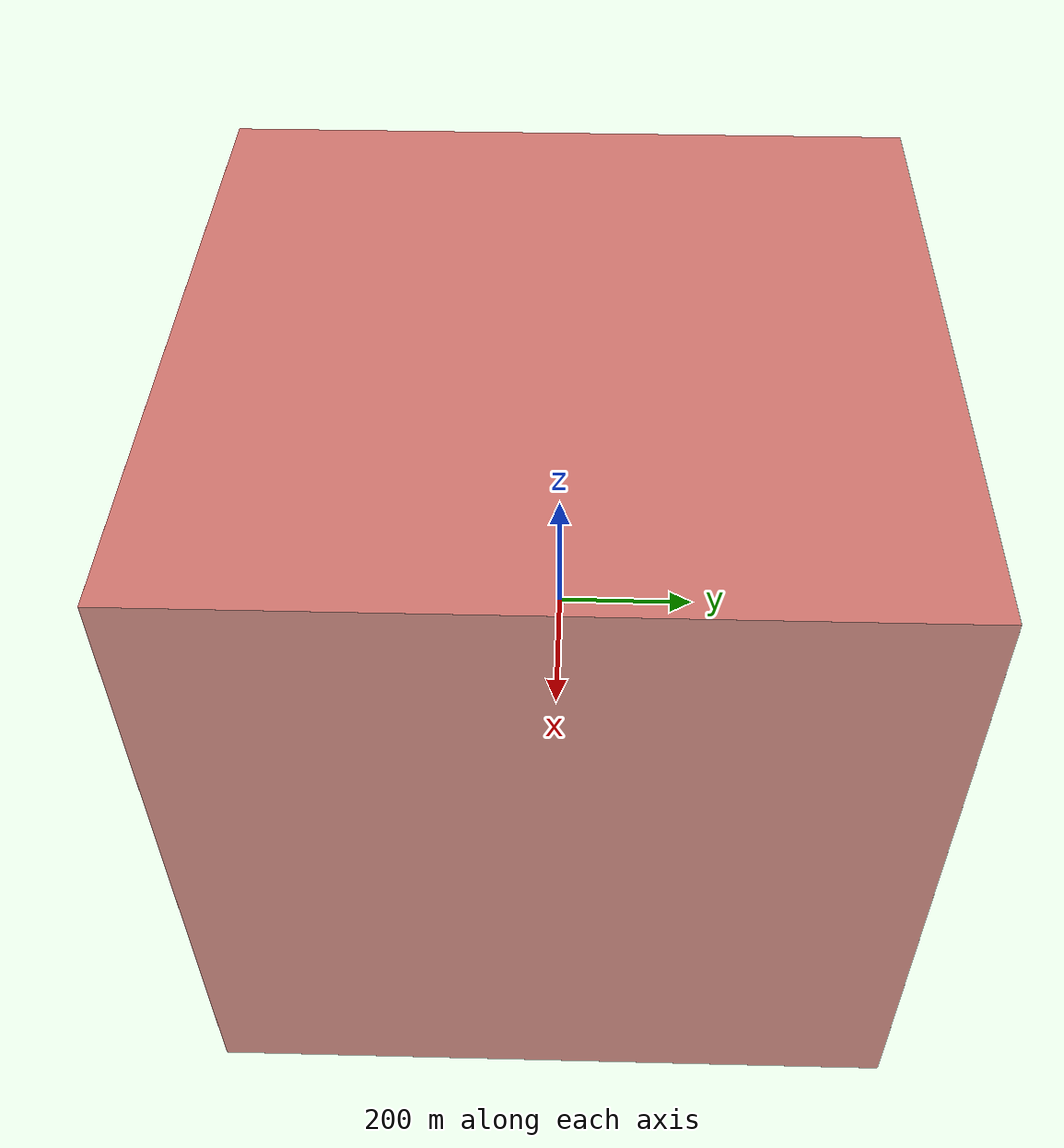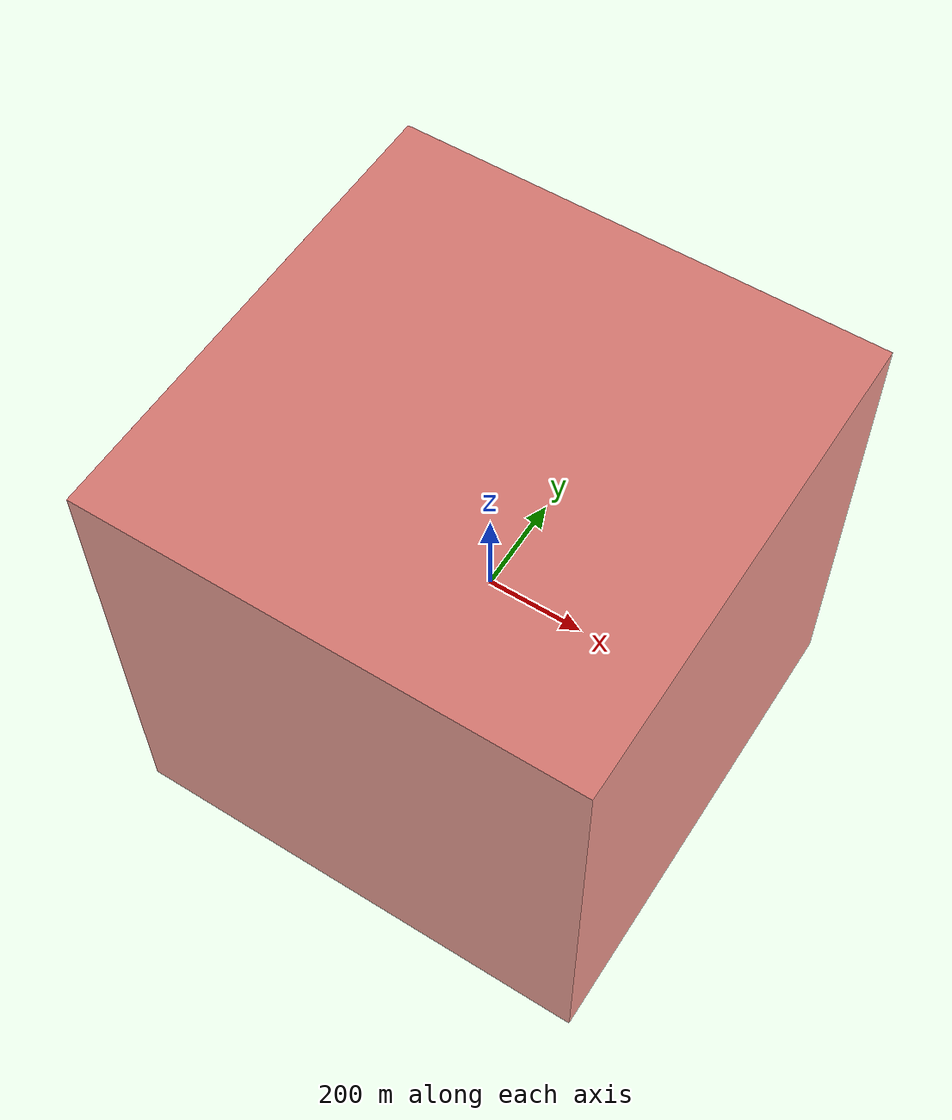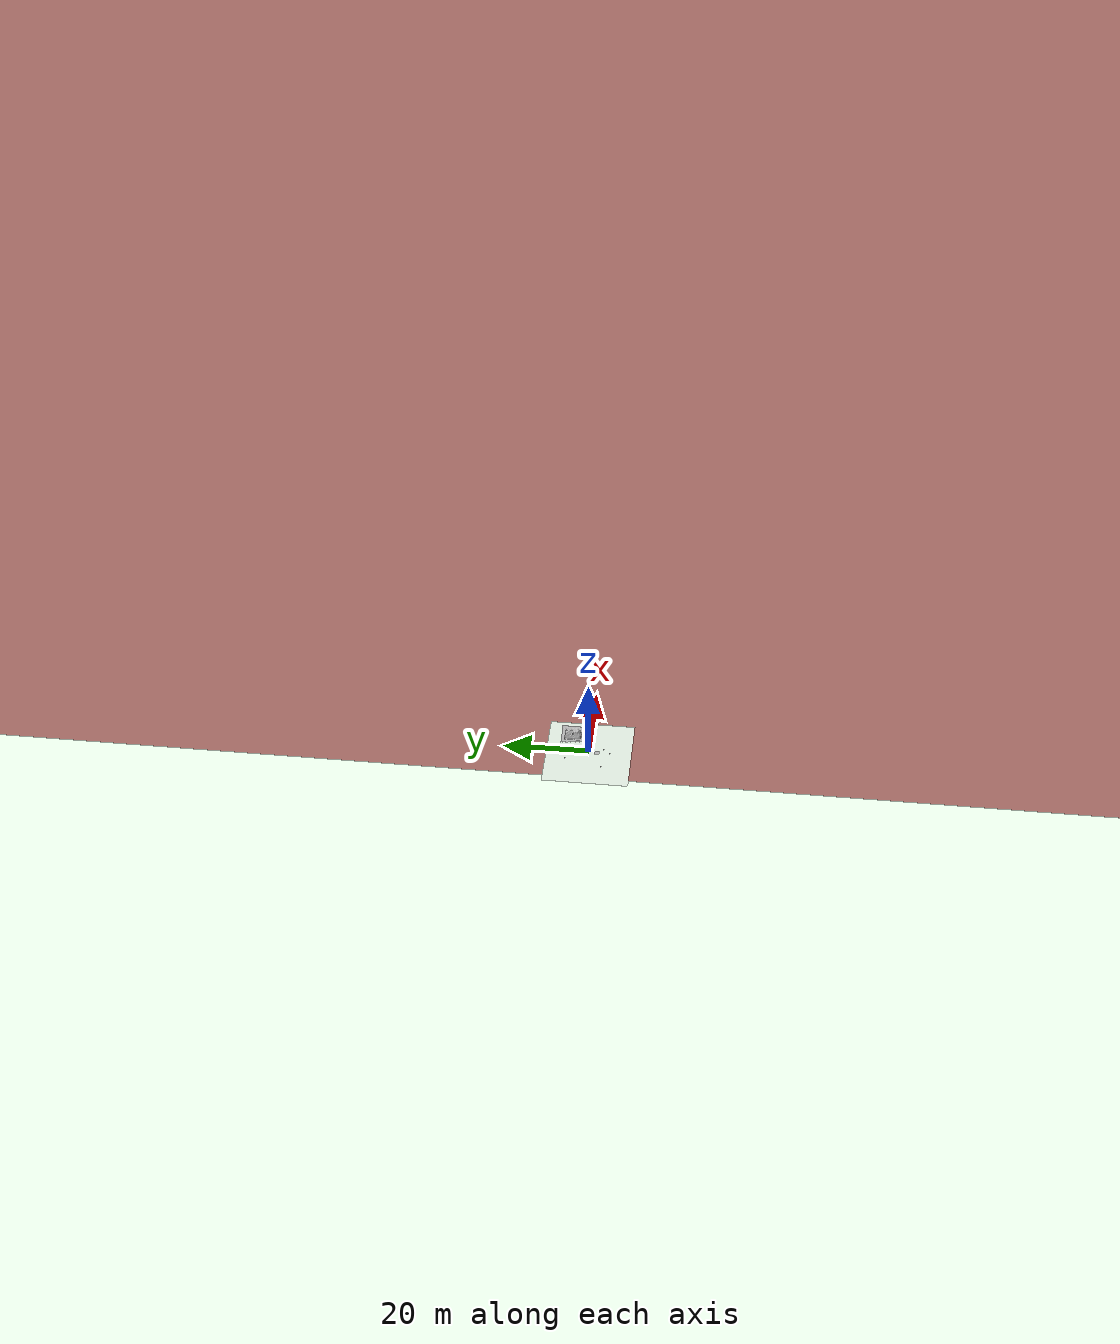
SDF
<sdf version="1.6">
 <world name="default">
  <light name="sun" type="directional">
   <pose>0 0 10 0 -0 0</pose>
   <diffuse>0.8 0.8 0.8 1</diffuse>
   <specular>0.1 0.1 0.1 1</specular>
   <attenuation>
    <range>1000</range>
    <constant>0.9</constant>
    <linear>0.01</linear>
    <quadratic>0.001</quadratic>
   </attenuation>
   <direction>-0.5 0.5 -1</direction>
  </light>
  <gravity>0 0 -9.8</gravity>
  <magnetic_field>6e-06 2.3e-05 -4.2e-05</magnetic_field>
  <atmosphere type="adiabatic"/>
  <physics name="default_physics" default="0" type="ode">
   <max_step_size>0.001</max_step_size>
   <real_time_factor>1</real_time_factor>
   <real_time_update_rate>1000</real_time_update_rate>
  </physics>
  <scene>
   <sky><clouds><speed>12</speed></clouds></sky>
   <ambient>0.4 0.4 0.4 1</ambient>
   <background>0.7 0.7 0.7 1</background>
   <shadows>1</shadows>
  </scene>
  <spherical_coordinates>
   <surface_model>EARTH_WGS84</surface_model>
   <latitude_deg>0</latitude_deg>
   <longitude_deg>0</longitude_deg>
   <elevation>0</elevation>
   <heading_deg>0</heading_deg>
  </spherical_coordinates>
  <model name="red_sky_filter">
   <link name="link_1">
    <visual name="visual1">
     <pose>-500 0 0 0 -0 1.5708</pose>
     <geometry><box><size>1000 0.1 1000</size></box></geometry>
     <material>
      <script><name>Gazebo/Red</name><uri>__default__</uri></script>
      <ambient>1 0 0 1</ambient>
      <diffuse>1 0 0 1</diffuse>
      <specular>1 0 0 1</specular>
      <emissive>1 0 0 1</emissive>
     </material>
     <transparency>0.4</transparency>
    </visual>
    <visual name="visual2">
     <pose>500 0 0 0 -0 1.5708</pose>
     <geometry><box><size>1000 0.1 1000</size></box></geometry>
     <material>
      <script><name>Gazebo/Red</name><uri>__default__</uri></script>
      <ambient>1 0 0 1</ambient>
      <diffuse>1 0 0 1</diffuse>
      <specular>1 0 0 1</specular>
      <emissive>1 0 0 1</emissive>
     </material>
     <transparency>0.4</transparency>
    </visual>
    <visual name="visual3">
     <pose>0 500 0 0 -0 0</pose>
     <geometry><box><size>1000 0.1 1000</size></box></geometry>
     <material>
      <script><name>Gazebo/Red</name><uri>__default__</uri></script>
      <ambient>1 0 0 1</ambient>
      <diffuse>1 0 0 1</diffuse>
      <specular>1 0 0 1</specular>
      <emissive>1 0 0 1</emissive>
     </material>
     <transparency>0.4</transparency>
    </visual>
    <visual name="visual4">
     <pose>0 -500 0 0 -0 0</pose>
     <geometry><box><size>1000 0.1 1000</size></box></geometry>
     <material>
      <script><name>Gazebo/Red</name><uri>__default__</uri></script>
      <ambient>1 0 0 1</ambient>
      <diffuse>1 0 0 1</diffuse>
      <specular>1 0 0 1</specular>
      <emissive>1 0 0 1</emissive>
     </material>
     <transparency>0.4</transparency>
    </visual>
    <visual name="visual5">
     <pose>0 0 500 0 -0 0</pose>
     <geometry><box><size>1000 1000 0.1</size></box></geometry>
     <material>
      <script><name>Gazebo/Red</name><uri>__default__</uri></script>
      <ambient>1 0 0 1</ambient>
      <diffuse>1 0 0 1</diffuse>
      <specular>1 0 0 1</specular>
      <emissive>1 0 0 1</emissive>
     </material>
     <transparency>0.4</transparency>
    </visual>
   </link>
   <static>1</static>
  </model>
  <model name="at0">
   <static>0</static>
   <link name="link">
    <inertial>
     <mass>0.01</mass>
     <inertia><ixx>4e-05</ixx><ixy>0</ixy><ixz>0</ixz><iyy>4e-05</iyy><iyz>0</iyz><izz>4e-05</izz></inertia>
    </inertial>
    <visual name="visual">
     <geometry><box><size>0.05 0.05 0.05</size></box></geometry>
     <material>
      <script>
       <uri>model://at0/materials/scripts</uri>
       <uri>model://at0/materials/textures</uri>
       <name>at0/Diffuse</name>
      </script>
     </material>
    </visual>
    <collision name="collision">
     <geometry><box><size>0.05 0.05 0.05</size></box></geometry>
     <surface><friction><ode><mu>0.8</mu><mu2>0.7</mu2></ode></friction></surface>
    </collision>
   </link>
   <pose>-6.40949 -0.430538 0.025 0 -0 0</pose>
  </model>
  <model name="at0_0">
   <static>0</static>
   <link name="link">
    <inertial>
     <mass>0.01</mass>
     <inertia><ixx>4e-05</ixx><ixy>0</ixy><ixz>0</ixz><iyy>4e-05</iyy><iyz>0</iyz><izz>4e-05</izz></inertia>
    </inertial>
    <visual name="visual">
     <geometry><box><size>0.05 0.05 0.05</size></box></geometry>
     <material>
      <script>
       <uri>model://at0/materials/scripts</uri>
       <uri>model://at0/materials/textures</uri>
       <name>at0/Diffuse</name>
      </script>
     </material>
    </visual>
    <collision name="collision">
     <geometry><box><size>0.05 0.05 0.05</size></box></geometry>
     <surface><friction><ode><mu>0.8</mu><mu2>0.7</mu2></ode></friction></surface>
    </collision>
   </link>
   <pose>-6.40589 -0.523574 0.025 0 -0 0</pose>
  </model>
  <model name="at0_1">
   <static>0</static>
   <link name="link">
    <inertial>
     <mass>0.01</mass>
     <inertia><ixx>4e-05</ixx><ixy>0</ixy><ixz>0</ixz><iyy>4e-05</iyy><iyz>0</iyz><izz>4e-05</izz></inertia>
    </inertial>
    <visual name="visual">
     <geometry><box><size>0.05 0.05 0.05</size></box></geometry>
     <material>
      <script>
       <uri>model://at0/materials/scripts</uri>
       <uri>model://at0/materials/textures</uri>
       <name>at0/Diffuse</name>
      </script>
     </material>
    </visual>
    <collision name="collision">
     <geometry><box><size>0.05 0.05 0.05</size></box></geometry>
     <surface><friction><ode><mu>0.8</mu><mu2>0.7</mu2></ode></friction></surface>
    </collision>
   </link>
   <pose>-6.49581 -0.5221 0.025 0 -0 0</pose>
  </model>
  <model name="at0_2">
   <static>0</static>
   <link name="link">
    <inertial>
     <mass>0.01</mass>
     <inertia><ixx>4e-05</ixx><ixy>0</ixy><ixz>0</ixz><iyy>4e-05</iyy><iyz>0</iyz><izz>4e-05</izz></inertia>
    </inertial>
    <visual name="visual">
     <geometry><box><size>0.05 0.05 0.05</size></box></geometry>
     <material>
      <script>
       <uri>model://at0/materials/scripts</uri>
       <uri>model://at0/materials/textures</uri>
       <name>at0/Diffuse</name>
      </script>
     </material>
    </visual>
    <collision name="collision">
     <geometry><box><size>0.05 0.05 0.05</size></box></geometry>
     <surface><friction><ode><mu>0.8</mu><mu2>0.7</mu2></ode></friction></surface>
    </collision>
   </link>
   <pose>-6.31735 -0.522905 0.025 0 -0 0</pose>
  </model>
  <model name="at0_3">
   <static>0</static>
   <link name="link">
    <inertial>
     <mass>0.01</mass>
     <inertia><ixx>4e-05</ixx><ixy>0</ixy><ixz>0</ixz><iyy>4e-05</iyy><iyz>0</iyz><izz>4e-05</izz></inertia>
    </inertial>
    <visual name="visual">
     <geometry><box><size>0.05 0.05 0.05</size></box></geometry>
     <material>
      <script>
       <uri>model://at0/materials/scripts</uri>
       <uri>model://at0/materials/textures</uri>
       <name>at0/Diffuse</name>
      </script>
     </material>
    </visual>
    <collision name="collision">
     <geometry><box><size>0.05 0.05 0.05</size></box></geometry>
     <surface><friction><ode><mu>0.8</mu><mu2>0.7</mu2></ode></friction></surface>
    </collision>
   </link>
   <pose>-6.49905 -0.428971 0.025 0 -0 0</pose>
  </model>
  <model name="at0_4">
   <static>0</static>
   <link name="link">
    <inertial>
     <mass>0.01</mass>
     <inertia><ixx>4e-05</ixx><ixy>0</ixy><ixz>0</ixz><iyy>4e-05</iyy><iyz>0</iyz><izz>4e-05</izz></inertia>
    </inertial>
    <visual name="visual">
     <geometry><box><size>0.05 0.05 0.05</size></box></geometry>
     <material>
      <script>
       <uri>model://at0/materials/scripts</uri>
       <uri>model://at0/materials/textures</uri>
       <name>at0/Diffuse</name>
      </script>
     </material>
    </visual>
    <collision name="collision">
     <geometry><box><size>0.05 0.05 0.05</size></box></geometry>
     <surface><friction><ode><mu>0.8</mu><mu2>0.7</mu2></ode></friction></surface>
    </collision>
   </link>
   <pose>-6.31512 -0.424897 0.025 0 -0 0</pose>
  </model>
  <model name="at0_5">
   <static>0</static>
   <link name="link">
    <inertial>
     <mass>0.01</mass>
     <inertia><ixx>4e-05</ixx><ixy>0</ixy><ixz>0</ixz><iyy>4e-05</iyy><iyz>0</iyz><izz>4e-05</izz></inertia>
    </inertial>
    <visual name="visual">
     <geometry><box><size>0.05 0.05 0.05</size></box></geometry>
     <material>
      <script>
       <uri>model://at0/materials/scripts</uri>
       <uri>model://at0/materials/textures</uri>
       <name>at0/Diffuse</name>
      </script>
     </material>
    </visual>
    <collision name="collision">
     <geometry><box><size>0.05 0.05 0.05</size></box></geometry>
     <surface><friction><ode><mu>0.8</mu><mu2>0.7</mu2></ode></friction></surface>
    </collision>
   </link>
   <pose>-6.50173 -0.322517 0.025 0 -0 0</pose>
  </model>
  <model name="at0_6">
   <static>0</static>
   <link name="link">
    <inertial>
     <mass>0.01</mass>
     <inertia><ixx>4e-05</ixx><ixy>0</ixy><ixz>0</ixz><iyy>4e-05</iyy><iyz>0</iyz><izz>4e-05</izz></inertia>
    </inertial>
    <visual name="visual">
     <geometry><box><size>0.05 0.05 0.05</size></box></geometry>
     <material>
      <script>
       <uri>model://at0/materials/scripts</uri>
       <uri>model://at0/materials/textures</uri>
       <name>at0/Diffuse</name>
      </script>
     </material>
    </visual>
    <collision name="collision">
     <geometry><box><size>0.05 0.05 0.05</size></box></geometry>
     <surface><friction><ode><mu>0.8</mu><mu2>0.7</mu2></ode></friction></surface>
    </collision>
   </link>
   <pose>-6.41147 -0.316812 0.025 0 -0 0</pose>
  </model>
  <model name="at0_7">
   <static>0</static>
   <link name="link">
    <inertial>
     <mass>0.01</mass>
     <inertia><ixx>4e-05</ixx><ixy>0</ixy><ixz>0</ixz><iyy>4e-05</iyy><iyz>0</iyz><izz>4e-05</izz></inertia>
    </inertial>
    <visual name="visual">
     <geometry><box><size>0.05 0.05 0.05</size></box></geometry>
     <material>
      <script>
       <uri>model://at0/materials/scripts</uri>
       <uri>model://at0/materials/textures</uri>
       <name>at0/Diffuse</name>
      </script>
     </material>
    </visual>
    <collision name="collision">
     <geometry><box><size>0.05 0.05 0.05</size></box></geometry>
     <surface><friction><ode><mu>0.8</mu><mu2>0.7</mu2></ode></friction></surface>
    </collision>
   </link>
   <pose>-6.31812 -0.321464 0.025 0 -0 0</pose>
  </model>
  <model name="at0_8">
   <static>0</static>
   <link name="link">
    <inertial>
     <mass>0.01</mass>
     <inertia><ixx>4e-05</ixx><ixy>0</ixy><ixz>0</ixz><iyy>4e-05</iyy><iyz>0</iyz><izz>4e-05</izz></inertia>
    </inertial>
    <visual name="visual">
     <geometry><box><size>0.05 0.05 0.05</size></box></geometry>
     <material>
      <script>
       <uri>model://at0/materials/scripts</uri>
       <uri>model://at0/materials/textures</uri>
       <name>at0/Diffuse</name>
      </script>
     </material>
    </visual>
    <collision name="collision">
     <geometry><box><size>0.05 0.05 0.05</size></box></geometry>
     <surface><friction><ode><mu>0.8</mu><mu2>0.7</mu2></ode></friction></surface>
    </collision>
   </link>
   <pose>4.36817 -4.50026 0.025 0 -0 0</pose>
  </model>
  <model name="at0_9">
   <static>0</static>
   <link name="link">
    <inertial>
     <mass>0.01</mass>
     <inertia><ixx>4e-05</ixx><ixy>0</ixy><ixz>0</ixz><iyy>4e-05</iyy><iyz>0</iyz><izz>4e-05</izz></inertia>
    </inertial>
    <visual name="visual">
     <geometry><box><size>0.05 0.05 0.05</size></box></geometry>
     <material>
      <script>
       <uri>model://at0/materials/scripts</uri>
       <uri>model://at0/materials/textures</uri>
       <name>at0/Diffuse</name>
      </script>
     </material>
    </visual>
    <collision name="collision">
     <geometry><box><size>0.05 0.05 0.05</size></box></geometry>
     <surface><friction><ode><mu>0.8</mu><mu2>0.7</mu2></ode></friction></surface>
    </collision>
   </link>
   <pose>4.44043 -4.56995 0.025 0 -0 0</pose>
  </model>
  <model name="at0_10">
   <static>0</static>
   <link name="link">
    <inertial>
     <mass>0.01</mass>
     <inertia><ixx>4e-05</ixx><ixy>0</ixy><ixz>0</ixz><iyy>4e-05</iyy><iyz>0</iyz><izz>4e-05</izz></inertia>
    </inertial>
    <visual name="visual">
     <geometry><box><size>0.05 0.05 0.05</size></box></geometry>
     <material>
      <script>
       <uri>model://at0/materials/scripts</uri>
       <uri>model://at0/materials/textures</uri>
       <name>at0/Diffuse</name>
      </script>
     </material>
    </visual>
    <collision name="collision">
     <geometry><box><size>0.05 0.05 0.05</size></box></geometry>
     <surface><friction><ode><mu>0.8</mu><mu2>0.7</mu2></ode></friction></surface>
    </collision>
   </link>
   <pose>4.52263 -4.64063 0.025 0 -0 0</pose>
  </model>
  <model name="at0_11">
   <static>0</static>
   <link name="link">
    <inertial>
     <mass>0.01</mass>
     <inertia><ixx>4e-05</ixx><ixy>0</ixy><ixz>0</ixz><iyy>4e-05</iyy><iyz>0</iyz><izz>4e-05</izz></inertia>
    </inertial>
    <visual name="visual">
     <geometry><box><size>0.05 0.05 0.05</size></box></geometry>
     <material>
      <script>
       <uri>model://at0/materials/scripts</uri>
       <uri>model://at0/materials/textures</uri>
       <name>at0/Diffuse</name>
      </script>
     </material>
    </visual>
    <collision name="collision">
     <geometry><box><size>0.05 0.05 0.05</size></box></geometry>
     <surface><friction><ode><mu>0.8</mu><mu2>0.7</mu2></ode></friction></surface>
    </collision>
   </link>
   <pose>4.60031 -4.71447 0.025 0 -0 0</pose>
  </model>
  <model name="at0_12">
   <static>0</static>
   <link name="link">
    <inertial>
     <mass>0.01</mass>
     <inertia><ixx>4e-05</ixx><ixy>0</ixy><ixz>0</ixz><iyy>4e-05</iyy><iyz>0</iyz><izz>4e-05</izz></inertia>
    </inertial>
    <visual name="visual">
     <geometry><box><size>0.05 0.05 0.05</size></box></geometry>
     <material>
      <script>
       <uri>model://at0/materials/scripts</uri>
       <uri>model://at0/materials/textures</uri>
       <name>at0/Diffuse</name>
      </script>
     </material>
    </visual>
    <collision name="collision">
     <geometry><box><size>0.05 0.05 0.05</size></box></geometry>
     <surface><friction><ode><mu>0.8</mu><mu2>0.7</mu2></ode></friction></surface>
    </collision>
   </link>
   <pose>5.00629 2.0256 0.025 0 -0 0</pose>
  </model>
  <model name="at0_13">
   <static>0</static>
   <link name="link">
    <inertial>
     <mass>0.01</mass>
     <inertia><ixx>4e-05</ixx><ixy>0</ixy><ixz>0</ixz><iyy>4e-05</iyy><iyz>0</iyz><izz>4e-05</izz></inertia>
    </inertial>
    <visual name="visual">
     <geometry><box><size>0.05 0.05 0.05</size></box></geometry>
     <material>
      <script>
       <uri>model://at0/materials/scripts</uri>
       <uri>model://at0/materials/textures</uri>
       <name>at0/Diffuse</name>
      </script>
     </material>
    </visual>
    <collision name="collision">
     <geometry><box><size>0.05 0.05 0.05</size></box></geometry>
     <surface><friction><ode><mu>0.8</mu><mu2>0.7</mu2></ode></friction></surface>
    </collision>
   </link>
   <pose>4.91775 2.0321 0.025 0 -0 0</pose>
  </model>
  <model name="at0_14">
   <static>0</static>
   <link name="link">
    <inertial>
     <mass>0.01</mass>
     <inertia><ixx>4e-05</ixx><ixy>0</ixy><ixz>0</ixz><iyy>4e-05</iyy><iyz>0</iyz><izz>4e-05</izz></inertia>
    </inertial>
    <visual name="visual">
     <geometry><box><size>0.05 0.05 0.05</size></box></geometry>
     <material>
      <script>
       <uri>model://at0/materials/scripts</uri>
       <uri>model://at0/materials/textures</uri>
       <name>at0/Diffuse</name>
      </script>
     </material>
    </visual>
    <collision name="collision">
     <geometry><box><size>0.05 0.05 0.05</size></box></geometry>
     <surface><friction><ode><mu>0.8</mu><mu2>0.7</mu2></ode></friction></surface>
    </collision>
   </link>
   <pose>5.11198 2.03767 0.025 0 -0 0</pose>
  </model>
  <model name="at0_15">
   <static>0</static>
   <link name="link">
    <inertial>
     <mass>0.01</mass>
     <inertia><ixx>4e-05</ixx><ixy>0</ixy><ixz>0</ixz><iyy>4e-05</iyy><iyz>0</iyz><izz>4e-05</izz></inertia>
    </inertial>
    <visual name="visual">
     <geometry><box><size>0.05 0.05 0.05</size></box></geometry>
     <material>
      <script>
       <uri>model://at0/materials/scripts</uri>
       <uri>model://at0/materials/textures</uri>
       <name>at0/Diffuse</name>
      </script>
     </material>
    </visual>
    <collision name="collision">
     <geometry><box><size>0.05 0.05 0.05</size></box></geometry>
     <surface><friction><ode><mu>0.8</mu><mu2>0.7</mu2></ode></friction></surface>
    </collision>
   </link>
   <pose>4.80952 2.03987 0.025 0 -0 0</pose>
  </model>
  <model name="at0_16">
   <static>0</static>
   <link name="link">
    <inertial>
     <mass>0.01</mass>
     <inertia><ixx>4e-05</ixx><ixy>0</ixy><ixz>0</ixz><iyy>4e-05</iyy><iyz>0</iyz><izz>4e-05</izz></inertia>
    </inertial>
    <visual name="visual">
     <geometry><box><size>0.05 0.05 0.05</size></box></geometry>
     <material>
      <script>
       <uri>model://at0/materials/scripts</uri>
       <uri>model://at0/materials/textures</uri>
       <name>at0/Diffuse</name>
      </script>
     </material>
    </visual>
    <collision name="collision">
     <geometry><box><size>0.05 0.05 0.05</size></box></geometry>
     <surface><friction><ode><mu>0.8</mu><mu2>0.7</mu2></ode></friction></surface>
    </collision>
   </link>
   <pose>5.20401 2.03143 0.025 0 -0 0</pose>
  </model>
  <model name="at0_17">
   <static>0</static>
   <link name="link">
    <inertial>
     <mass>0.01</mass>
     <inertia><ixx>4e-05</ixx><ixy>0</ixy><ixz>0</ixz><iyy>4e-05</iyy><iyz>0</iyz><izz>4e-05</izz></inertia>
    </inertial>
    <visual name="visual">
     <geometry><box><size>0.05 0.05 0.05</size></box></geometry>
     <material>
      <script>
       <uri>model://at0/materials/scripts</uri>
       <uri>model://at0/materials/textures</uri>
       <name>at0/Diffuse</name>
      </script>
     </material>
    </visual>
    <collision name="collision">
     <geometry><box><size>0.05 0.05 0.05</size></box></geometry>
     <surface><friction><ode><mu>0.8</mu><mu2>0.7</mu2></ode></friction></surface>
    </collision>
   </link>
   <pose>5.00356 1.91692 0.025 0 -0 0</pose>
  </model>
  <model name="at0_18">
   <static>0</static>
   <link name="link">
    <inertial>
     <mass>0.01</mass>
     <inertia><ixx>4e-05</ixx><ixy>0</ixy><ixz>0</ixz><iyy>4e-05</iyy><iyz>0</iyz><izz>4e-05</izz></inertia>
    </inertial>
    <visual name="visual">
     <geometry><box><size>0.05 0.05 0.05</size></box></geometry>
     <material>
      <script>
       <uri>model://at0/materials/scripts</uri>
       <uri>model://at0/materials/textures</uri>
       <name>at0/Diffuse</name>
      </script>
     </material>
    </visual>
    <collision name="collision">
     <geometry><box><size>0.05 0.05 0.05</size></box></geometry>
     <surface><friction><ode><mu>0.8</mu><mu2>0.7</mu2></ode></friction></surface>
    </collision>
   </link>
   <pose>5.01128 2.14067 0.025 0 -0 0</pose>
  </model>
  <model name="at0_19">
   <static>0</static>
   <link name="link">
    <inertial>
     <mass>0.01</mass>
     <inertia><ixx>4e-05</ixx><ixy>0</ixy><ixz>0</ixz><iyy>4e-05</iyy><iyz>0</iyz><izz>4e-05</izz></inertia>
    </inertial>
    <visual name="visual">
     <geometry><box><size>0.05 0.05 0.05</size></box></geometry>
     <material>
      <script>
       <uri>model://at0/materials/scripts</uri>
       <uri>model://at0/materials/textures</uri>
       <name>at0/Diffuse</name>
      </script>
     </material>
    </visual>
    <collision name="collision">
     <geometry><box><size>0.05 0.05 0.05</size></box></geometry>
     <surface><friction><ode><mu>0.8</mu><mu2>0.7</mu2></ode></friction></surface>
    </collision>
   </link>
   <pose>5.01094 1.8122 0.025 0 -0 0</pose>
  </model>
  <model name="at0_20">
   <static>0</static>
   <link name="link">
    <inertial>
     <mass>0.01</mass>
     <inertia><ixx>4e-05</ixx><ixy>0</ixy><ixz>0</ixz><iyy>4e-05</iyy><iyz>0</iyz><izz>4e-05</izz></inertia>
    </inertial>
    <visual name="visual">
     <geometry><box><size>0.05 0.05 0.05</size></box></geometry>
     <material>
      <script>
       <uri>model://at0/materials/scripts</uri>
       <uri>model://at0/materials/textures</uri>
       <name>at0/Diffuse</name>
      </script>
     </material>
    </visual>
    <collision name="collision">
     <geometry><box><size>0.05 0.05 0.05</size></box></geometry>
     <surface><friction><ode><mu>0.8</mu><mu2>0.7</mu2></ode></friction></surface>
    </collision>
   </link>
   <pose>5.01438 2.26492 0.025 0 -0 0</pose>
  </model>
  <model name="at0_21">
   <static>0</static>
   <link name="link">
    <inertial>
     <mass>0.01</mass>
     <inertia><ixx>4e-05</ixx><ixy>0</ixy><ixz>0</ixz><iyy>4e-05</iyy><iyz>0</iyz><izz>4e-05</izz></inertia>
    </inertial>
    <visual name="visual">
     <geometry><box><size>0.05 0.05 0.05</size></box></geometry>
     <material>
      <script>
       <uri>model://at0/materials/scripts</uri>
       <uri>model://at0/materials/textures</uri>
       <name>at0/Diffuse</name>
      </script>
     </material>
    </visual>
    <collision name="collision">
     <geometry><box><size>0.05 0.05 0.05</size></box></geometry>
     <surface><friction><ode><mu>0.8</mu><mu2>0.7</mu2></ode></friction></surface>
    </collision>
   </link>
   <pose>4.9246 2.1401 0.025 0 -0 0</pose>
  </model>
  <model name="at0_22">
   <static>0</static>
   <link name="link">
    <inertial>
     <mass>0.01</mass>
     <inertia><ixx>4e-05</ixx><ixy>0</ixy><ixz>0</ixz><iyy>4e-05</iyy><iyz>0</iyz><izz>4e-05</izz></inertia>
    </inertial>
    <visual name="visual">
     <geometry><box><size>0.05 0.05 0.05</size></box></geometry>
     <material>
      <script>
       <uri>model://at0/materials/scripts</uri>
       <uri>model://at0/materials/textures</uri>
       <name>at0/Diffuse</name>
      </script>
     </material>
    </visual>
    <collision name="collision">
     <geometry><box><size>0.05 0.05 0.05</size></box></geometry>
     <surface><friction><ode><mu>0.8</mu><mu2>0.7</mu2></ode></friction></surface>
    </collision>
   </link>
   <pose>4.83085 2.28629 0.025 0 -0 0</pose>
  </model>
  <model name="at0_23">
   <static>0</static>
   <link name="link">
    <inertial>
     <mass>0.01</mass>
     <inertia><ixx>4e-05</ixx><ixy>0</ixy><ixz>0</ixz><iyy>4e-05</iyy><iyz>0</iyz><izz>4e-05</izz></inertia>
    </inertial>
    <visual name="visual">
     <geometry><box><size>0.05 0.05 0.05</size></box></geometry>
     <material>
      <script>
       <uri>model://at0/materials/scripts</uri>
       <uri>model://at0/materials/textures</uri>
       <name>at0/Diffuse</name>
      </script>
     </material>
    </visual>
    <collision name="collision">
     <geometry><box><size>0.05 0.05 0.05</size></box></geometry>
     <surface><friction><ode><mu>0.8</mu><mu2>0.7</mu2></ode></friction></surface>
    </collision>
   </link>
   <pose>5.1022 1.92591 0.025 0 -0 0</pose>
  </model>
  <model name="at0_24">
   <static>0</static>
   <link name="link">
    <inertial>
     <mass>0.01</mass>
     <inertia><ixx>4e-05</ixx><ixy>0</ixy><ixz>0</ixz><iyy>4e-05</iyy><iyz>0</iyz><izz>4e-05</izz></inertia>
    </inertial>
    <visual name="visual">
     <geometry><box><size>0.05 0.05 0.05</size></box></geometry>
     <material>
      <script>
       <uri>model://at0/materials/scripts</uri>
       <uri>model://at0/materials/textures</uri>
       <name>at0/Diffuse</name>
      </script>
     </material>
    </visual>
    <collision name="collision">
     <geometry><box><size>0.05 0.05 0.05</size></box></geometry>
     <surface><friction><ode><mu>0.8</mu><mu2>0.7</mu2></ode></friction></surface>
    </collision>
   </link>
   <pose>5.18728 1.8004 0.025 0 -0 0</pose>
  </model>
  <model name="at0_25">
   <static>0</static>
   <link name="link">
    <inertial>
     <mass>0.01</mass>
     <inertia><ixx>4e-05</ixx><ixy>0</ixy><ixz>0</ixz><iyy>4e-05</iyy><iyz>0</iyz><izz>4e-05</izz></inertia>
    </inertial>
    <visual name="visual">
     <geometry><box><size>0.05 0.05 0.05</size></box></geometry>
     <material>
      <script>
       <uri>model://at0/materials/scripts</uri>
       <uri>model://at0/materials/textures</uri>
       <name>at0/Diffuse</name>
      </script>
     </material>
    </visual>
    <collision name="collision">
     <geometry><box><size>0.05 0.05 0.05</size></box></geometry>
     <surface><friction><ode><mu>0.8</mu><mu2>0.7</mu2></ode></friction></surface>
    </collision>
   </link>
   <pose>4.81081 1.80355 0.025 0 -0 0</pose>
  </model>
  <model name="at0_26">
   <static>0</static>
   <link name="link">
    <inertial>
     <mass>0.01</mass>
     <inertia><ixx>4e-05</ixx><ixy>0</ixy><ixz>0</ixz><iyy>4e-05</iyy><iyz>0</iyz><izz>4e-05</izz></inertia>
    </inertial>
    <visual name="visual">
     <geometry><box><size>0.05 0.05 0.05</size></box></geometry>
     <material>
      <script>
       <uri>model://at0/materials/scripts</uri>
       <uri>model://at0/materials/textures</uri>
       <name>at0/Diffuse</name>
      </script>
     </material>
    </visual>
    <collision name="collision">
     <geometry><box><size>0.05 0.05 0.05</size></box></geometry>
     <surface><friction><ode><mu>0.8</mu><mu2>0.7</mu2></ode></friction></surface>
    </collision>
   </link>
   <pose>4.90711 1.93152 0.025 0 -0 0</pose>
  </model>
  <model name="at0_27">
   <static>0</static>
   <link name="link">
    <inertial>
     <mass>0.01</mass>
     <inertia><ixx>4e-05</ixx><ixy>0</ixy><ixz>0</ixz><iyy>4e-05</iyy><iyz>0</iyz><izz>4e-05</izz></inertia>
    </inertial>
    <visual name="visual">
     <geometry><box><size>0.05 0.05 0.05</size></box></geometry>
     <material>
      <script>
       <uri>model://at0/materials/scripts</uri>
       <uri>model://at0/materials/textures</uri>
       <name>at0/Diffuse</name>
      </script>
     </material>
    </visual>
    <collision name="collision">
     <geometry><box><size>0.05 0.05 0.05</size></box></geometry>
     <surface><friction><ode><mu>0.8</mu><mu2>0.7</mu2></ode></friction></surface>
    </collision>
   </link>
   <pose>5.0998 2.13918 0.025 0 -0 0</pose>
  </model>
  <model name="at0_28">
   <static>0</static>
   <link name="link">
    <inertial>
     <mass>0.01</mass>
     <inertia><ixx>4e-05</ixx><ixy>0</ixy><ixz>0</ixz><iyy>4e-05</iyy><iyz>0</iyz><izz>4e-05</izz></inertia>
    </inertial>
    <visual name="visual">
     <geometry><box><size>0.05 0.05 0.05</size></box></geometry>
     <material>
      <script>
       <uri>model://at0/materials/scripts</uri>
       <uri>model://at0/materials/textures</uri>
       <name>at0/Diffuse</name>
      </script>
     </material>
    </visual>
    <collision name="collision">
     <geometry><box><size>0.05 0.05 0.05</size></box></geometry>
     <surface><friction><ode><mu>0.8</mu><mu2>0.7</mu2></ode></friction></surface>
    </collision>
   </link>
   <pose>4.81998 2.15685 0.025 0 -0 0</pose>
  </model>
  <model name="at0_29">
   <static>0</static>
   <link name="link">
    <inertial>
     <mass>0.01</mass>
     <inertia><ixx>4e-05</ixx><ixy>0</ixy><ixz>0</ixz><iyy>4e-05</iyy><iyz>0</iyz><izz>4e-05</izz></inertia>
    </inertial>
    <visual name="visual">
     <geometry><box><size>0.05 0.05 0.05</size></box></geometry>
     <material>
      <script>
       <uri>model://at0/materials/scripts</uri>
       <uri>model://at0/materials/textures</uri>
       <name>at0/Diffuse</name>
      </script>
     </material>
    </visual>
    <collision name="collision">
     <geometry><box><size>0.05 0.05 0.05</size></box></geometry>
     <surface><friction><ode><mu>0.8</mu><mu2>0.7</mu2></ode></friction></surface>
    </collision>
   </link>
   <pose>4.81855 1.92091 0.025 0 -0 0</pose>
  </model>
  <model name="at0_30">
   <static>0</static>
   <link name="link">
    <inertial>
     <mass>0.01</mass>
     <inertia><ixx>4e-05</ixx><ixy>0</ixy><ixz>0</ixz><iyy>4e-05</iyy><iyz>0</iyz><izz>4e-05</izz></inertia>
    </inertial>
    <visual name="visual">
     <geometry><box><size>0.05 0.05 0.05</size></box></geometry>
     <material>
      <script>
       <uri>model://at0/materials/scripts</uri>
       <uri>model://at0/materials/textures</uri>
       <name>at0/Diffuse</name>
      </script>
     </material>
    </visual>
    <collision name="collision">
     <geometry><box><size>0.05 0.05 0.05</size></box></geometry>
     <surface><friction><ode><mu>0.8</mu><mu2>0.7</mu2></ode></friction></surface>
    </collision>
   </link>
   <pose>4.90694 1.80076 0.025 0 -0 0</pose>
  </model>
  <model name="at0_31">
   <static>0</static>
   <link name="link">
    <inertial>
     <mass>0.01</mass>
     <inertia><ixx>4e-05</ixx><ixy>0</ixy><ixz>0</ixz><iyy>4e-05</iyy><iyz>0</iyz><izz>4e-05</izz></inertia>
    </inertial>
    <visual name="visual">
     <geometry><box><size>0.05 0.05 0.05</size></box></geometry>
     <material>
      <script>
       <uri>model://at0/materials/scripts</uri>
       <uri>model://at0/materials/textures</uri>
       <name>at0/Diffuse</name>
      </script>
     </material>
    </visual>
    <collision name="collision">
     <geometry><box><size>0.05 0.05 0.05</size></box></geometry>
     <surface><friction><ode><mu>0.8</mu><mu2>0.7</mu2></ode></friction></surface>
    </collision>
   </link>
   <pose>4.92745 2.27021 0.025 0 -0 0</pose>
  </model>
  <model name="at0_32">
   <static>0</static>
   <link name="link">
    <inertial>
     <mass>0.01</mass>
     <inertia><ixx>4e-05</ixx><ixy>0</ixy><ixz>0</ixz><iyy>4e-05</iyy><iyz>0</iyz><izz>4e-05</izz></inertia>
    </inertial>
    <visual name="visual">
     <geometry><box><size>0.05 0.05 0.05</size></box></geometry>
     <material>
      <script>
       <uri>model://at0/materials/scripts</uri>
       <uri>model://at0/materials/textures</uri>
       <name>at0/Diffuse</name>
      </script>
     </material>
    </visual>
    <collision name="collision">
     <geometry><box><size>0.05 0.05 0.05</size></box></geometry>
     <surface><friction><ode><mu>0.8</mu><mu2>0.7</mu2></ode></friction></surface>
    </collision>
   </link>
   <pose>5.11949 2.27753 0.025 0 -0 0</pose>
  </model>
  <model name="at0_33">
   <static>0</static>
   <link name="link">
    <inertial>
     <mass>0.01</mass>
     <inertia><ixx>4e-05</ixx><ixy>0</ixy><ixz>0</ixz><iyy>4e-05</iyy><iyz>0</iyz><izz>4e-05</izz></inertia>
    </inertial>
    <visual name="visual">
     <geometry><box><size>0.05 0.05 0.05</size></box></geometry>
     <material>
      <script>
       <uri>model://at0/materials/scripts</uri>
       <uri>model://at0/materials/textures</uri>
       <name>at0/Diffuse</name>
      </script>
     </material>
    </visual>
    <collision name="collision">
     <geometry><box><size>0.05 0.05 0.05</size></box></geometry>
     <surface><friction><ode><mu>0.8</mu><mu2>0.7</mu2></ode></friction></surface>
    </collision>
   </link>
   <pose>5.10254 1.80744 0.025 0 -0 0</pose>
  </model>
  <model name="at0_34">
   <static>0</static>
   <link name="link">
    <inertial>
     <mass>0.01</mass>
     <inertia><ixx>4e-05</ixx><ixy>0</ixy><ixz>0</ixz><iyy>4e-05</iyy><iyz>0</iyz><izz>4e-05</izz></inertia>
    </inertial>
    <visual name="visual">
     <geometry><box><size>0.05 0.05 0.05</size></box></geometry>
     <material>
      <script>
       <uri>model://at0/materials/scripts</uri>
       <uri>model://at0/materials/textures</uri>
       <name>at0/Diffuse</name>
      </script>
     </material>
    </visual>
    <collision name="collision">
     <geometry><box><size>0.05 0.05 0.05</size></box></geometry>
     <surface><friction><ode><mu>0.8</mu><mu2>0.7</mu2></ode></friction></surface>
    </collision>
   </link>
   <pose>5.20563 2.14353 0.025 0 -0 0</pose>
  </model>
  <model name="at0_35">
   <static>0</static>
   <link name="link">
    <inertial>
     <mass>0.01</mass>
     <inertia><ixx>4e-05</ixx><ixy>0</ixy><ixz>0</ixz><iyy>4e-05</iyy><iyz>0</iyz><izz>4e-05</izz></inertia>
    </inertial>
    <visual name="visual">
     <geometry><box><size>0.05 0.05 0.05</size></box></geometry>
     <material>
      <script>
       <uri>model://at0/materials/scripts</uri>
       <uri>model://at0/materials/textures</uri>
       <name>at0/Diffuse</name>
      </script>
     </material>
    </visual>
    <collision name="collision">
     <geometry><box><size>0.05 0.05 0.05</size></box></geometry>
     <surface><friction><ode><mu>0.8</mu><mu2>0.7</mu2></ode></friction></surface>
    </collision>
   </link>
   <pose>5.21715 2.27576 0.025 0 -0 0</pose>
  </model>
  <model name="at0_36">
   <static>0</static>
   <link name="link">
    <inertial>
     <mass>0.01</mass>
     <inertia><ixx>4e-05</ixx><ixy>0</ixy><ixz>0</ixz><iyy>4e-05</iyy><iyz>0</iyz><izz>4e-05</izz></inertia>
    </inertial>
    <visual name="visual">
     <geometry><box><size>0.05 0.05 0.05</size></box></geometry>
     <material>
      <script>
       <uri>model://at0/materials/scripts</uri>
       <uri>model://at0/materials/textures</uri>
       <name>at0/Diffuse</name>
      </script>
     </material>
    </visual>
    <collision name="collision">
     <geometry><box><size>0.05 0.05 0.05</size></box></geometry>
     <surface><friction><ode><mu>0.8</mu><mu2>0.7</mu2></ode></friction></surface>
    </collision>
   </link>
   <pose>5.19848 1.92752 0.025 0 -0 0</pose>
  </model>
  <model name="at0_37">
   <static>0</static>
   <link name="link">
    <inertial>
     <mass>0.01</mass>
     <inertia><ixx>4e-05</ixx><ixy>0</ixy><ixz>0</ixz><iyy>4e-05</iyy><iyz>0</iyz><izz>4e-05</izz></inertia>
    </inertial>
    <visual name="visual">
     <geometry><box><size>0.05 0.05 0.05</size></box></geometry>
     <material>
      <script>
       <uri>model://at0/materials/scripts</uri>
       <uri>model://at0/materials/textures</uri>
       <name>at0/Diffuse</name>
      </script>
     </material>
    </visual>
    <collision name="collision">
     <geometry><box><size>0.05 0.05 0.05</size></box></geometry>
     <surface><friction><ode><mu>0.8</mu><mu2>0.7</mu2></ode></friction></surface>
    </collision>
   </link>
   <pose>-4.6907 -3.52832 0.025 0 -0 0</pose>
  </model>
  <model name="at0_38">
   <static>0</static>
   <link name="link">
    <inertial>
     <mass>0.01</mass>
     <inertia><ixx>4e-05</ixx><ixy>0</ixy><ixz>0</ixz><iyy>4e-05</iyy><iyz>0</iyz><izz>4e-05</izz></inertia>
    </inertial>
    <visual name="visual">
     <geometry><box><size>0.05 0.05 0.05</size></box></geometry>
     <material>
      <script>
       <uri>model://at0/materials/scripts</uri>
       <uri>model://at0/materials/textures</uri>
       <name>at0/Diffuse</name>
      </script>
     </material>
    </visual>
    <collision name="collision">
     <geometry><box><size>0.05 0.05 0.05</size></box></geometry>
     <surface><friction><ode><mu>0.8</mu><mu2>0.7</mu2></ode></friction></surface>
    </collision>
   </link>
   <pose>-4.81131 -3.51441 0.025 0 -0 0</pose>
  </model>
  <model name="at0_39">
   <static>0</static>
   <link name="link">
    <inertial>
     <mass>0.01</mass>
     <inertia><ixx>4e-05</ixx><ixy>0</ixy><ixz>0</ixz><iyy>4e-05</iyy><iyz>0</iyz><izz>4e-05</izz></inertia>
    </inertial>
    <visual name="visual">
     <geometry><box><size>0.05 0.05 0.05</size></box></geometry>
     <material>
      <script>
       <uri>model://at0/materials/scripts</uri>
       <uri>model://at0/materials/textures</uri>
       <name>at0/Diffuse</name>
      </script>
     </material>
    </visual>
    <collision name="collision">
     <geometry><box><size>0.05 0.05 0.05</size></box></geometry>
     <surface><friction><ode><mu>0.8</mu><mu2>0.7</mu2></ode></friction></surface>
    </collision>
   </link>
   <pose>-4.81026 -3.65293 0.025 0 -0 0</pose>
  </model>
  <model name="at0_40">
   <static>0</static>
   <link name="link">
    <inertial>
     <mass>0.01</mass>
     <inertia><ixx>4e-05</ixx><ixy>0</ixy><ixz>0</ixz><iyy>4e-05</iyy><iyz>0</iyz><izz>4e-05</izz></inertia>
    </inertial>
    <visual name="visual">
     <geometry><box><size>0.05 0.05 0.05</size></box></geometry>
     <material>
      <script>
       <uri>model://at0/materials/scripts</uri>
       <uri>model://at0/materials/textures</uri>
       <name>at0/Diffuse</name>
      </script>
     </material>
    </visual>
    <collision name="collision">
     <geometry><box><size>0.05 0.05 0.05</size></box></geometry>
     <surface><friction><ode><mu>0.8</mu><mu2>0.7</mu2></ode></friction></surface>
    </collision>
   </link>
   <pose>-4.68218 -3.65703 0.025 0 -0 0</pose>
  </model>
  <model name="at0_41">
   <static>0</static>
   <link name="link">
    <inertial>
     <mass>0.01</mass>
     <inertia><ixx>4e-05</ixx><ixy>0</ixy><ixz>0</ixz><iyy>4e-05</iyy><iyz>0</iyz><izz>4e-05</izz></inertia>
    </inertial>
    <visual name="visual">
     <geometry><box><size>0.05 0.05 0.05</size></box></geometry>
     <material>
      <script>
       <uri>model://at0/materials/scripts</uri>
       <uri>model://at0/materials/textures</uri>
       <name>at0/Diffuse</name>
      </script>
     </material>
    </visual>
    <collision name="collision">
     <geometry><box><size>0.05 0.05 0.05</size></box></geometry>
     <surface><friction><ode><mu>0.8</mu><mu2>0.7</mu2></ode></friction></surface>
    </collision>
   </link>
   <pose>-4.55928 -3.51068 0.025 0 -0 0</pose>
  </model>
  <model name="at0_42">
   <static>0</static>
   <link name="link">
    <inertial>
     <mass>0.01</mass>
     <inertia><ixx>4e-05</ixx><ixy>0</ixy><ixz>0</ixz><iyy>4e-05</iyy><iyz>0</iyz><izz>4e-05</izz></inertia>
    </inertial>
    <visual name="visual">
     <geometry><box><size>0.05 0.05 0.05</size></box></geometry>
     <material>
      <script>
       <uri>model://at0/materials/scripts</uri>
       <uri>model://at0/materials/textures</uri>
       <name>at0/Diffuse</name>
      </script>
     </material>
    </visual>
    <collision name="collision">
     <geometry><box><size>0.05 0.05 0.05</size></box></geometry>
     <surface><friction><ode><mu>0.8</mu><mu2>0.7</mu2></ode></friction></surface>
    </collision>
   </link>
   <pose>-4.55718 -3.63593 0.025 0 -0 0</pose>
  </model>
  <model name="at0_43">
   <static>0</static>
   <link name="link">
    <inertial>
     <mass>0.01</mass>
     <inertia><ixx>4e-05</ixx><ixy>0</ixy><ixz>0</ixz><iyy>4e-05</iyy><iyz>0</iyz><izz>4e-05</izz></inertia>
    </inertial>
    <visual name="visual">
     <geometry><box><size>0.05 0.05 0.05</size></box></geometry>
     <material>
      <script>
       <uri>model://at0/materials/scripts</uri>
       <uri>model://at0/materials/textures</uri>
       <name>at0/Diffuse</name>
      </script>
     </material>
    </visual>
    <collision name="collision">
     <geometry><box><size>0.05 0.05 0.05</size></box></geometry>
     <surface><friction><ode><mu>0.8</mu><mu2>0.7</mu2></ode></friction></surface>
    </collision>
   </link>
   <pose>-4.82807 -3.33909 0.025 0 -0 0</pose>
  </model>
  <model name="at0_44">
   <static>0</static>
   <link name="link">
    <inertial>
     <mass>0.01</mass>
     <inertia><ixx>4e-05</ixx><ixy>0</ixy><ixz>0</ixz><iyy>4e-05</iyy><iyz>0</iyz><izz>4e-05</izz></inertia>
    </inertial>
    <visual name="visual">
     <geometry><box><size>0.05 0.05 0.05</size></box></geometry>
     <material>
      <script>
       <uri>model://at0/materials/scripts</uri>
       <uri>model://at0/materials/textures</uri>
       <name>at0/Diffuse</name>
      </script>
     </material>
    </visual>
    <collision name="collision">
     <geometry><box><size>0.05 0.05 0.05</size></box></geometry>
     <surface><friction><ode><mu>0.8</mu><mu2>0.7</mu2></ode></friction></surface>
    </collision>
   </link>
   <pose>-4.70447 -3.35388 0.025 0 -0 0</pose>
  </model>
  <model name="at0_45">
   <static>0</static>
   <link name="link">
    <inertial>
     <mass>0.01</mass>
     <inertia><ixx>4e-05</ixx><ixy>0</ixy><ixz>0</ixz><iyy>4e-05</iyy><iyz>0</iyz><izz>4e-05</izz></inertia>
    </inertial>
    <visual name="visual">
     <geometry><box><size>0.05 0.05 0.05</size></box></geometry>
     <material>
      <script>
       <uri>model://at0/materials/scripts</uri>
       <uri>model://at0/materials/textures</uri>
       <name>at0/Diffuse</name>
      </script>
     </material>
    </visual>
    <collision name="collision">
     <geometry><box><size>0.05 0.05 0.05</size></box></geometry>
     <surface><friction><ode><mu>0.8</mu><mu2>0.7</mu2></ode></friction></surface>
    </collision>
   </link>
   <pose>-4.57929 -3.35469 0.025 0 -0 0</pose>
  </model>
  <model name="at0_46">
   <static>0</static>
   <link name="link">
    <inertial>
     <mass>0.01</mass>
     <inertia><ixx>4e-05</ixx><ixy>0</ixy><ixz>0</ixz><iyy>4e-05</iyy><iyz>0</iyz><izz>4e-05</izz></inertia>
    </inertial>
    <visual name="visual">
     <geometry><box><size>0.05 0.05 0.05</size></box></geometry>
     <material>
      <script>
       <uri>model://at0/materials/scripts</uri>
       <uri>model://at0/materials/textures</uri>
       <name>at0/Diffuse</name>
      </script>
     </material>
    </visual>
    <collision name="collision">
     <geometry><box><size>0.05 0.05 0.05</size></box></geometry>
     <surface><friction><ode><mu>0.8</mu><mu2>0.7</mu2></ode></friction></surface>
    </collision>
   </link>
   <pose>4.43499 -4.48652 0.025 0 -0 0</pose>
  </model>
  <model name="at0_47">
   <static>0</static>
   <link name="link">
    <inertial>
     <mass>0.01</mass>
     <inertia><ixx>4e-05</ixx><ixy>0</ixy><ixz>0</ixz><iyy>4e-05</iyy><iyz>0</iyz><izz>4e-05</izz></inertia>
    </inertial>
    <visual name="visual">
     <geometry><box><size>0.05 0.05 0.05</size></box></geometry>
     <material>
      <script>
       <uri>model://at0/materials/scripts</uri>
       <uri>model://at0/materials/textures</uri>
       <name>at0/Diffuse</name>
      </script>
     </material>
    </visual>
    <collision name="collision">
     <geometry><box><size>0.05 0.05 0.05</size></box></geometry>
     <surface><friction><ode><mu>0.8</mu><mu2>0.7</mu2></ode></friction></surface>
    </collision>
   </link>
   <pose>4.52162 -4.56224 0.025 0 -0 0</pose>
  </model>
  <model name="at0_48">
   <static>0</static>
   <link name="link">
    <inertial>
     <mass>0.01</mass>
     <inertia><ixx>4e-05</ixx><ixy>0</ixy><ixz>0</ixz><iyy>4e-05</iyy><iyz>0</iyz><izz>4e-05</izz></inertia>
    </inertial>
    <visual name="visual">
     <geometry><box><size>0.05 0.05 0.05</size></box></geometry>
     <material>
      <script>
       <uri>model://at0/materials/scripts</uri>
       <uri>model://at0/materials/textures</uri>
       <name>at0/Diffuse</name>
      </script>
     </material>
    </visual>
    <collision name="collision">
     <geometry><box><size>0.05 0.05 0.05</size></box></geometry>
     <surface><friction><ode><mu>0.8</mu><mu2>0.7</mu2></ode></friction></surface>
    </collision>
   </link>
   <pose>4.5975 -4.63307 0.025 0 -0 0</pose>
  </model>
  <model name="at0_49">
   <static>0</static>
   <link name="link">
    <inertial>
     <mass>0.01</mass>
     <inertia><ixx>4e-05</ixx><ixy>0</ixy><ixz>0</ixz><iyy>4e-05</iyy><iyz>0</iyz><izz>4e-05</izz></inertia>
    </inertial>
    <visual name="visual">
     <geometry><box><size>0.05 0.05 0.05</size></box></geometry>
     <material>
      <script>
       <uri>model://at0/materials/scripts</uri>
       <uri>model://at0/materials/textures</uri>
       <name>at0/Diffuse</name>
      </script>
     </material>
    </visual>
    <collision name="collision">
     <geometry><box><size>0.05 0.05 0.05</size></box></geometry>
     <surface><friction><ode><mu>0.8</mu><mu2>0.7</mu2></ode></friction></surface>
    </collision>
   </link>
   <pose>4.68158 -4.71094 0.025 0 -0 0</pose>
  </model>
  <model name="at0_50">
   <static>0</static>
   <link name="link">
    <inertial>
     <mass>0.01</mass>
     <inertia><ixx>4e-05</ixx><ixy>0</ixy><ixz>0</ixz><iyy>4e-05</iyy><iyz>0</iyz><izz>4e-05</izz></inertia>
    </inertial>
    <visual name="visual">
     <geometry><box><size>0.05 0.05 0.05</size></box></geometry>
     <material>
      <script>
       <uri>model://at0/materials/scripts</uri>
       <uri>model://at0/materials/textures</uri>
       <name>at0/Diffuse</name>
      </script>
     </material>
    </visual>
    <collision name="collision">
     <geometry><box><size>0.05 0.05 0.05</size></box></geometry>
     <surface><friction><ode><mu>0.8</mu><mu2>0.7</mu2></ode></friction></surface>
    </collision>
   </link>
   <pose>4.68395 -4.78159 0.025 0 -0 0</pose>
  </model>
  <model name="at0_51">
   <static>0</static>
   <link name="link">
    <inertial>
     <mass>0.01</mass>
     <inertia><ixx>4e-05</ixx><ixy>0</ixy><ixz>0</ixz><iyy>4e-05</iyy><iyz>0</iyz><izz>4e-05</izz></inertia>
    </inertial>
    <visual name="visual">
     <geometry><box><size>0.05 0.05 0.05</size></box></geometry>
     <material>
      <script>
       <uri>model://at0/materials/scripts</uri>
       <uri>model://at0/materials/textures</uri>
       <name>at0/Diffuse</name>
      </script>
     </material>
    </visual>
    <collision name="collision">
     <geometry><box><size>0.05 0.05 0.05</size></box></geometry>
     <surface><friction><ode><mu>0.8</mu><mu2>0.7</mu2></ode></friction></surface>
    </collision>
   </link>
   <pose>-4.16222 -5.34635 0.025 0 -0 0</pose>
  </model>
  <model name="at0_52">
   <static>0</static>
   <link name="link">
    <inertial>
     <mass>0.01</mass>
     <inertia><ixx>4e-05</ixx><ixy>0</ixy><ixz>0</ixz><iyy>4e-05</iyy><iyz>0</iyz><izz>4e-05</izz></inertia>
    </inertial>
    <visual name="visual">
     <geometry><box><size>0.05 0.05 0.05</size></box></geometry>
     <material>
      <script>
       <uri>model://at0/materials/scripts</uri>
       <uri>model://at0/materials/textures</uri>
       <name>at0/Diffuse</name>
      </script>
     </material>
    </visual>
    <collision name="collision">
     <geometry><box><size>0.05 0.05 0.05</size></box></geometry>
     <surface><friction><ode><mu>0.8</mu><mu2>0.7</mu2></ode></friction></surface>
    </collision>
   </link>
   <pose>-4.0634 -5.34856 0.025 0 -0 0</pose>
  </model>
  <model name="at0_53">
   <static>0</static>
   <link name="link">
    <inertial>
     <mass>0.01</mass>
     <inertia><ixx>4e-05</ixx><ixy>0</ixy><ixz>0</ixz><iyy>4e-05</iyy><iyz>0</iyz><izz>4e-05</izz></inertia>
    </inertial>
    <visual name="visual">
     <geometry><box><size>0.05 0.05 0.05</size></box></geometry>
     <material>
      <script>
       <uri>model://at0/materials/scripts</uri>
       <uri>model://at0/materials/textures</uri>
       <name>at0/Diffuse</name>
      </script>
     </material>
    </visual>
    <collision name="collision">
     <geometry><box><size>0.05 0.05 0.05</size></box></geometry>
     <surface><friction><ode><mu>0.8</mu><mu2>0.7</mu2></ode></friction></surface>
    </collision>
   </link>
   <pose>-4.16454 -5.45616 0.025 0 -0 0</pose>
  </model>
  <model name="at0_54">
   <static>0</static>
   <link name="link">
    <inertial>
     <mass>0.01</mass>
     <inertia><ixx>4e-05</ixx><ixy>0</ixy><ixz>0</ixz><iyy>4e-05</iyy><iyz>0</iyz><izz>4e-05</izz></inertia>
    </inertial>
    <visual name="visual">
     <geometry><box><size>0.05 0.05 0.05</size></box></geometry>
     <material>
      <script>
       <uri>model://at0/materials/scripts</uri>
       <uri>model://at0/materials/textures</uri>
       <name>at0/Diffuse</name>
      </script>
     </material>
    </visual>
    <collision name="collision">
     <geometry><box><size>0.05 0.05 0.05</size></box></geometry>
     <surface><friction><ode><mu>0.8</mu><mu2>0.7</mu2></ode></friction></surface>
    </collision>
   </link>
   <pose>-4.07058 -5.45552 0.025 0 -0 0</pose>
  </model>
  <model name="at0_55">
   <static>0</static>
   <link name="link">
    <inertial>
     <mass>0.01</mass>
     <inertia><ixx>4e-05</ixx><ixy>0</ixy><ixz>0</ixz><iyy>4e-05</iyy><iyz>0</iyz><izz>4e-05</izz></inertia>
    </inertial>
    <visual name="visual">
     <geometry><box><size>0.05 0.05 0.05</size></box></geometry>
     <material>
      <script>
       <uri>model://at0/materials/scripts</uri>
       <uri>model://at0/materials/textures</uri>
       <name>at0/Diffuse</name>
      </script>
     </material>
    </visual>
    <collision name="collision">
     <geometry><box><size>0.05 0.05 0.05</size></box></geometry>
     <surface><friction><ode><mu>0.8</mu><mu2>0.7</mu2></ode></friction></surface>
    </collision>
   </link>
   <pose>-2.56579 5.37796 0.025 0 -0 0</pose>
  </model>
  <model name="at0_56">
   <static>0</static>
   <link name="link">
    <inertial>
     <mass>0.01</mass>
     <inertia><ixx>4e-05</ixx><ixy>0</ixy><ixz>0</ixz><iyy>4e-05</iyy><iyz>0</iyz><izz>4e-05</izz></inertia>
    </inertial>
    <visual name="visual">
     <geometry><box><size>0.05 0.05 0.05</size></box></geometry>
     <material>
      <script>
       <uri>model://at0/materials/scripts</uri>
       <uri>model://at0/materials/textures</uri>
       <name>at0/Diffuse</name>
      </script>
     </material>
    </visual>
    <collision name="collision">
     <geometry><box><size>0.05 0.05 0.05</size></box></geometry>
     <surface><friction><ode><mu>0.8</mu><mu2>0.7</mu2></ode></friction></surface>
    </collision>
   </link>
   <pose>-2.46785 5.39426 0.025 0 -0 0</pose>
  </model>
  <model name="at0_57">
   <static>0</static>
   <link name="link">
    <inertial>
     <mass>0.01</mass>
     <inertia><ixx>4e-05</ixx><ixy>0</ixy><ixz>0</ixz><iyy>4e-05</iyy><iyz>0</iyz><izz>4e-05</izz></inertia>
    </inertial>
    <visual name="visual">
     <geometry><box><size>0.05 0.05 0.05</size></box></geometry>
     <material>
      <script>
       <uri>model://at0/materials/scripts</uri>
       <uri>model://at0/materials/textures</uri>
       <name>at0/Diffuse</name>
      </script>
     </material>
    </visual>
    <collision name="collision">
     <geometry><box><size>0.05 0.05 0.05</size></box></geometry>
     <surface><friction><ode><mu>0.8</mu><mu2>0.7</mu2></ode></friction></surface>
    </collision>
   </link>
   <pose>-2.35325 5.37789 0.025 0 -0 0</pose>
  </model>
  <model name="at0_58">
   <static>0</static>
   <link name="link">
    <inertial>
     <mass>0.01</mass>
     <inertia><ixx>4e-05</ixx><ixy>0</ixy><ixz>0</ixz><iyy>4e-05</iyy><iyz>0</iyz><izz>4e-05</izz></inertia>
    </inertial>
    <visual name="visual">
     <geometry><box><size>0.05 0.05 0.05</size></box></geometry>
     <material>
      <script>
       <uri>model://at0/materials/scripts</uri>
       <uri>model://at0/materials/textures</uri>
       <name>at0/Diffuse</name>
      </script>
     </material>
    </visual>
    <collision name="collision">
     <geometry><box><size>0.05 0.05 0.05</size></box></geometry>
     <surface><friction><ode><mu>0.8</mu><mu2>0.7</mu2></ode></friction></surface>
    </collision>
   </link>
   <pose>-2.56467 5.25392 0.025 0 -0 0</pose>
  </model>
  <model name="at0_59">
   <static>0</static>
   <link name="link">
    <inertial>
     <mass>0.01</mass>
     <inertia><ixx>4e-05</ixx><ixy>0</ixy><ixz>0</ixz><iyy>4e-05</iyy><iyz>0</iyz><izz>4e-05</izz></inertia>
    </inertial>
    <visual name="visual">
     <geometry><box><size>0.05 0.05 0.05</size></box></geometry>
     <material>
      <script>
       <uri>model://at0/materials/scripts</uri>
       <uri>model://at0/materials/textures</uri>
       <name>at0/Diffuse</name>
      </script>
     </material>
    </visual>
    <collision name="collision">
     <geometry><box><size>0.05 0.05 0.05</size></box></geometry>
     <surface><friction><ode><mu>0.8</mu><mu2>0.7</mu2></ode></friction></surface>
    </collision>
   </link>
   <pose>-2.45158 5.25697 0.025 0 -0 0</pose>
  </model>
  <model name="at0_60">
   <static>0</static>
   <link name="link">
    <inertial>
     <mass>0.01</mass>
     <inertia><ixx>4e-05</ixx><ixy>0</ixy><ixz>0</ixz><iyy>4e-05</iyy><iyz>0</iyz><izz>4e-05</izz></inertia>
    </inertial>
    <visual name="visual">
     <geometry><box><size>0.05 0.05 0.05</size></box></geometry>
     <material>
      <script>
       <uri>model://at0/materials/scripts</uri>
       <uri>model://at0/materials/textures</uri>
       <name>at0/Diffuse</name>
      </script>
     </material>
    </visual>
    <collision name="collision">
     <geometry><box><size>0.05 0.05 0.05</size></box></geometry>
     <surface><friction><ode><mu>0.8</mu><mu2>0.7</mu2></ode></friction></surface>
    </collision>
   </link>
   <pose>-2.34864 5.25448 0.025 0 -0 0</pose>
  </model>
  <model name="at0_61">
   <static>0</static>
   <link name="link">
    <inertial>
     <mass>0.01</mass>
     <inertia><ixx>4e-05</ixx><ixy>0</ixy><ixz>0</ixz><iyy>4e-05</iyy><iyz>0</iyz><izz>4e-05</izz></inertia>
    </inertial>
    <visual name="visual">
     <geometry><box><size>0.05 0.05 0.05</size></box></geometry>
     <material>
      <script>
       <uri>model://at0/materials/scripts</uri>
       <uri>model://at0/materials/textures</uri>
       <name>at0/Diffuse</name>
      </script>
     </material>
    </visual>
    <collision name="collision">
     <geometry><box><size>0.05 0.05 0.05</size></box></geometry>
     <surface><friction><ode><mu>0.8</mu><mu2>0.7</mu2></ode></friction></surface>
    </collision>
   </link>
   <pose>-1.17407 5.77775 0.025 0 -0 0</pose>
  </model>
  <model name="at0_62">
   <static>0</static>
   <link name="link">
    <inertial>
     <mass>0.01</mass>
     <inertia><ixx>4e-05</ixx><ixy>0</ixy><ixz>0</ixz><iyy>4e-05</iyy><iyz>0</iyz><izz>4e-05</izz></inertia>
    </inertial>
    <visual name="visual">
     <geometry><box><size>0.05 0.05 0.05</size></box></geometry>
     <material>
      <script>
       <uri>model://at0/materials/scripts</uri>
       <uri>model://at0/materials/textures</uri>
       <name>at0/Diffuse</name>
      </script>
     </material>
    </visual>
    <collision name="collision">
     <geometry><box><size>0.05 0.05 0.05</size></box></geometry>
     <surface><friction><ode><mu>0.8</mu><mu2>0.7</mu2></ode></friction></surface>
    </collision>
   </link>
   <pose>-1.17237 5.6844 0.025 0 -0 0</pose>
  </model>
  <model name="at0_63">
   <static>0</static>
   <link name="link">
    <inertial>
     <mass>0.01</mass>
     <inertia><ixx>4e-05</ixx><ixy>0</ixy><ixz>0</ixz><iyy>4e-05</iyy><iyz>0</iyz><izz>4e-05</izz></inertia>
    </inertial>
    <visual name="visual">
     <geometry><box><size>0.05 0.05 0.05</size></box></geometry>
     <material>
      <script>
       <uri>model://at0/materials/scripts</uri>
       <uri>model://at0/materials/textures</uri>
       <name>at0/Diffuse</name>
      </script>
     </material>
    </visual>
    <collision name="collision">
     <geometry><box><size>0.05 0.05 0.05</size></box></geometry>
     <surface><friction><ode><mu>0.8</mu><mu2>0.7</mu2></ode></friction></surface>
    </collision>
   </link>
   <pose>-1.25785 5.78169 0.025 0 -0 0</pose>
  </model>
  <model name="at0_64">
   <static>0</static>
   <link name="link">
    <inertial>
     <mass>0.01</mass>
     <inertia><ixx>4e-05</ixx><ixy>0</ixy><ixz>0</ixz><iyy>4e-05</iyy><iyz>0</iyz><izz>4e-05</izz></inertia>
    </inertial>
    <visual name="visual">
     <geometry><box><size>0.05 0.05 0.05</size></box></geometry>
     <material>
      <script>
       <uri>model://at0/materials/scripts</uri>
       <uri>model://at0/materials/textures</uri>
       <name>at0/Diffuse</name>
      </script>
     </material>
    </visual>
    <collision name="collision">
     <geometry><box><size>0.05 0.05 0.05</size></box></geometry>
     <surface><friction><ode><mu>0.8</mu><mu2>0.7</mu2></ode></friction></surface>
    </collision>
   </link>
   <pose>-1.26189 5.67858 0.025 0 -0 0</pose>
  </model>
  <model name="at0_65">
   <static>0</static>
   <link name="link">
    <inertial>
     <mass>0.01</mass>
     <inertia><ixx>4e-05</ixx><ixy>0</ixy><ixz>0</ixz><iyy>4e-05</iyy><iyz>0</iyz><izz>4e-05</izz></inertia>
    </inertial>
    <visual name="visual">
     <geometry><box><size>0.05 0.05 0.05</size></box></geometry>
     <material>
      <script>
       <uri>model://at0/materials/scripts</uri>
       <uri>model://at0/materials/textures</uri>
       <name>at0/Diffuse</name>
      </script>
     </material>
    </visual>
    <collision name="collision">
     <geometry><box><size>0.05 0.05 0.05</size></box></geometry>
     <surface><friction><ode><mu>0.8</mu><mu2>0.7</mu2></ode></friction></surface>
    </collision>
   </link>
   <pose>5.72216 -0.983534 0.025 0 -0 0</pose>
  </model>
  <model name="at0_66">
   <static>0</static>
   <link name="link">
    <inertial>
     <mass>0.01</mass>
     <inertia><ixx>4e-05</ixx><ixy>0</ixy><ixz>0</ixz><iyy>4e-05</iyy><iyz>0</iyz><izz>4e-05</izz></inertia>
    </inertial>
    <visual name="visual">
     <geometry><box><size>0.05 0.05 0.05</size></box></geometry>
     <material>
      <script>
       <uri>model://at0/materials/scripts</uri>
       <uri>model://at0/materials/textures</uri>
       <name>at0/Diffuse</name>
      </script>
     </material>
    </visual>
    <collision name="collision">
     <geometry><box><size>0.05 0.05 0.05</size></box></geometry>
     <surface><friction><ode><mu>0.8</mu><mu2>0.7</mu2></ode></friction></surface>
    </collision>
   </link>
   <pose>2.19747 -0.068983 0.025 0 -0 0</pose>
  </model>
  <model name="at0_67">
   <static>0</static>
   <link name="link">
    <inertial>
     <mass>0.01</mass>
     <inertia><ixx>4e-05</ixx><ixy>0</ixy><ixz>0</ixz><iyy>4e-05</iyy><iyz>0</iyz><izz>4e-05</izz></inertia>
    </inertial>
    <visual name="visual">
     <geometry><box><size>0.05 0.05 0.05</size></box></geometry>
     <material>
      <script>
       <uri>model://at0/materials/scripts</uri>
       <uri>model://at0/materials/textures</uri>
       <name>at0/Diffuse</name>
      </script>
     </material>
    </visual>
    <collision name="collision">
     <geometry><box><size>0.05 0.05 0.05</size></box></geometry>
     <surface><friction><ode><mu>0.8</mu><mu2>0.7</mu2></ode></friction></surface>
    </collision>
   </link>
   <pose>1.95407 -0.83089 0.025 0 -0 0</pose>
  </model>
  <model name="at0_68">
   <static>0</static>
   <link name="link">
    <inertial>
     <mass>0.01</mass>
     <inertia><ixx>4e-05</ixx><ixy>0</ixy><ixz>0</ixz><iyy>4e-05</iyy><iyz>0</iyz><izz>4e-05</izz></inertia>
    </inertial>
    <visual name="visual">
     <geometry><box><size>0.05 0.05 0.05</size></box></geometry>
     <material>
      <script>
       <uri>model://at0/materials/scripts</uri>
       <uri>model://at0/materials/textures</uri>
       <name>at0/Diffuse</name>
      </script>
     </material>
    </visual>
    <collision name="collision">
     <geometry><box><size>0.05 0.05 0.05</size></box></geometry>
     <surface><friction><ode><mu>0.8</mu><mu2>0.7</mu2></ode></friction></surface>
    </collision>
   </link>
   <pose>1.78831 0.249803 0.025 0 -0 0</pose>
  </model>
  <model name="at0_69">
   <static>0</static>
   <link name="link">
    <inertial>
     <mass>0.01</mass>
     <inertia><ixx>4e-05</ixx><ixy>0</ixy><ixz>0</ixz><iyy>4e-05</iyy><iyz>0</iyz><izz>4e-05</izz></inertia>
    </inertial>
    <visual name="visual">
     <geometry><box><size>0.05 0.05 0.05</size></box></geometry>
     <material>
      <script>
       <uri>model://at0/materials/scripts</uri>
       <uri>model://at0/materials/textures</uri>
       <name>at0/Diffuse</name>
      </script>
     </material>
    </visual>
    <collision name="collision">
     <geometry><box><size>0.05 0.05 0.05</size></box></geometry>
     <surface><friction><ode><mu>0.8</mu><mu2>0.7</mu2></ode></friction></surface>
    </collision>
   </link>
   <pose>1.93499 -0.108598 0.025 0 -0 0</pose>
  </model>
  <model name="at0_70">
   <static>0</static>
   <link name="link">
    <inertial>
     <mass>0.01</mass>
     <inertia><ixx>4e-05</ixx><ixy>0</ixy><ixz>0</ixz><iyy>4e-05</iyy><iyz>0</iyz><izz>4e-05</izz></inertia>
    </inertial>
    <visual name="visual">
     <geometry><box><size>0.05 0.05 0.05</size></box></geometry>
     <material>
      <script>
       <uri>model://at0/materials/scripts</uri>
       <uri>model://at0/materials/textures</uri>
       <name>at0/Diffuse</name>
      </script>
     </material>
    </visual>
    <collision name="collision">
     <geometry><box><size>0.05 0.05 0.05</size></box></geometry>
     <surface><friction><ode><mu>0.8</mu><mu2>0.7</mu2></ode></friction></surface>
    </collision>
   </link>
   <pose>2.00894 0.141349 0.025 0 -0 0</pose>
  </model>
  <model name="at0_71">
   <static>0</static>
   <link name="link">
    <inertial>
     <mass>0.01</mass>
     <inertia><ixx>4e-05</ixx><ixy>0</ixy><ixz>0</ixz><iyy>4e-05</iyy><iyz>0</iyz><izz>4e-05</izz></inertia>
    </inertial>
    <visual name="visual">
     <geometry><box><size>0.05 0.05 0.05</size></box></geometry>
     <material>
      <script>
       <uri>model://at0/materials/scripts</uri>
       <uri>model://at0/materials/textures</uri>
       <name>at0/Diffuse</name>
      </script>
     </material>
    </visual>
    <collision name="collision">
     <geometry><box><size>0.05 0.05 0.05</size></box></geometry>
     <surface><friction><ode><mu>0.8</mu><mu2>0.7</mu2></ode></friction></surface>
    </collision>
   </link>
   <pose>1.9953 5.26682 0.025 0 -0 0</pose>
  </model>
  <model name="at0_72">
   <static>0</static>
   <link name="link">
    <inertial>
     <mass>0.01</mass>
     <inertia><ixx>4e-05</ixx><ixy>0</ixy><ixz>0</ixz><iyy>4e-05</iyy><iyz>0</iyz><izz>4e-05</izz></inertia>
    </inertial>
    <visual name="visual">
     <geometry><box><size>0.05 0.05 0.05</size></box></geometry>
     <material>
      <script>
       <uri>model://at0/materials/scripts</uri>
       <uri>model://at0/materials/textures</uri>
       <name>at0/Diffuse</name>
      </script>
     </material>
    </visual>
    <collision name="collision">
     <geometry><box><size>0.05 0.05 0.05</size></box></geometry>
     <surface><friction><ode><mu>0.8</mu><mu2>0.7</mu2></ode></friction></surface>
    </collision>
   </link>
   <pose>2.06028 5.19131 0.025 0 -0 0</pose>
  </model>
  <model name="at0_73">
   <static>0</static>
   <link name="link">
    <inertial>
     <mass>0.01</mass>
     <inertia><ixx>4e-05</ixx><ixy>0</ixy><ixz>0</ixz><iyy>4e-05</iyy><iyz>0</iyz><izz>4e-05</izz></inertia>
    </inertial>
    <visual name="visual">
     <geometry><box><size>0.05 0.05 0.05</size></box></geometry>
     <material>
      <script>
       <uri>model://at0/materials/scripts</uri>
       <uri>model://at0/materials/textures</uri>
       <name>at0/Diffuse</name>
      </script>
     </material>
    </visual>
    <collision name="collision">
     <geometry><box><size>0.05 0.05 0.05</size></box></geometry>
     <surface><friction><ode><mu>0.8</mu><mu2>0.7</mu2></ode></friction></surface>
    </collision>
   </link>
   <pose>2.05735 5.10511 0.025 0 -0 0</pose>
  </model>
  <model name="at0_74">
   <static>0</static>
   <link name="link">
    <inertial>
     <mass>0.01</mass>
     <inertia><ixx>4e-05</ixx><ixy>0</ixy><ixz>0</ixz><iyy>4e-05</iyy><iyz>0</iyz><izz>4e-05</izz></inertia>
    </inertial>
    <visual name="visual">
     <geometry><box><size>0.05 0.05 0.05</size></box></geometry>
     <material>
      <script>
       <uri>model://at0/materials/scripts</uri>
       <uri>model://at0/materials/textures</uri>
       <name>at0/Diffuse</name>
      </script>
     </material>
    </visual>
    <collision name="collision">
     <geometry><box><size>0.05 0.05 0.05</size></box></geometry>
     <surface><friction><ode><mu>0.8</mu><mu2>0.7</mu2></ode></friction></surface>
    </collision>
   </link>
   <pose>2.11482 5.02602 0.025 0 -0 0</pose>
  </model>
  <model name="at0_75">
   <static>0</static>
   <link name="link">
    <inertial>
     <mass>0.01</mass>
     <inertia><ixx>4e-05</ixx><ixy>0</ixy><ixz>0</ixz><iyy>4e-05</iyy><iyz>0</iyz><izz>4e-05</izz></inertia>
    </inertial>
    <visual name="visual">
     <geometry><box><size>0.05 0.05 0.05</size></box></geometry>
     <material>
      <script>
       <uri>model://at0/materials/scripts</uri>
       <uri>model://at0/materials/textures</uri>
       <name>at0/Diffuse</name>
      </script>
     </material>
    </visual>
    <collision name="collision">
     <geometry><box><size>0.05 0.05 0.05</size></box></geometry>
     <surface><friction><ode><mu>0.8</mu><mu2>0.7</mu2></ode></friction></surface>
    </collision>
   </link>
   <pose>-4.50537 2.49759 0.025 0 -0 0</pose>
  </model>
  <model name="at0_76">
   <static>0</static>
   <link name="link">
    <inertial>
     <mass>0.01</mass>
     <inertia><ixx>4e-05</ixx><ixy>0</ixy><ixz>0</ixz><iyy>4e-05</iyy><iyz>0</iyz><izz>4e-05</izz></inertia>
    </inertial>
    <visual name="visual">
     <geometry><box><size>0.05 0.05 0.05</size></box></geometry>
     <material>
      <script>
       <uri>model://at0/materials/scripts</uri>
       <uri>model://at0/materials/textures</uri>
       <name>at0/Diffuse</name>
      </script>
     </material>
    </visual>
    <collision name="collision">
     <geometry><box><size>0.05 0.05 0.05</size></box></geometry>
     <surface><friction><ode><mu>0.8</mu><mu2>0.7</mu2></ode></friction></surface>
    </collision>
   </link>
   <pose>-4.33232 2.63554 0.025 0 -0 0</pose>
  </model>
  <model name="at0_77">
   <static>0</static>
   <link name="link">
    <inertial>
     <mass>0.01</mass>
     <inertia><ixx>4e-05</ixx><ixy>0</ixy><ixz>0</ixz><iyy>4e-05</iyy><iyz>0</iyz><izz>4e-05</izz></inertia>
    </inertial>
    <visual name="visual">
     <geometry><box><size>0.05 0.05 0.05</size></box></geometry>
     <material>
      <script>
       <uri>model://at0/materials/scripts</uri>
       <uri>model://at0/materials/textures</uri>
       <name>at0/Diffuse</name>
      </script>
     </material>
    </visual>
    <collision name="collision">
     <geometry><box><size>0.05 0.05 0.05</size></box></geometry>
     <surface><friction><ode><mu>0.8</mu><mu2>0.7</mu2></ode></friction></surface>
    </collision>
   </link>
   <pose>-4.1491 2.81536 0.025 0 -0 0</pose>
  </model>
  <model name="at0_78">
   <static>0</static>
   <link name="link">
    <inertial>
     <mass>0.01</mass>
     <inertia><ixx>4e-05</ixx><ixy>0</ixy><ixz>0</ixz><iyy>4e-05</iyy><iyz>0</iyz><izz>4e-05</izz></inertia>
    </inertial>
    <visual name="visual">
     <geometry><box><size>0.05 0.05 0.05</size></box></geometry>
     <material>
      <script>
       <uri>model://at0/materials/scripts</uri>
       <uri>model://at0/materials/textures</uri>
       <name>at0/Diffuse</name>
      </script>
     </material>
    </visual>
    <collision name="collision">
     <geometry><box><size>0.05 0.05 0.05</size></box></geometry>
     <surface><friction><ode><mu>0.8</mu><mu2>0.7</mu2></ode></friction></surface>
    </collision>
   </link>
   <pose>-4.01136 3.05335 0.025 0 -0 0</pose>
  </model>
  <model name="at0_79">
   <static>0</static>
   <link name="link">
    <inertial>
     <mass>0.01</mass>
     <inertia><ixx>4e-05</ixx><ixy>0</ixy><ixz>0</ixz><iyy>4e-05</iyy><iyz>0</iyz><izz>4e-05</izz></inertia>
    </inertial>
    <visual name="visual">
     <geometry><box><size>0.05 0.05 0.05</size></box></geometry>
     <material>
      <script>
       <uri>model://at0/materials/scripts</uri>
       <uri>model://at0/materials/textures</uri>
       <name>at0/Diffuse</name>
      </script>
     </material>
    </visual>
    <collision name="collision">
     <geometry><box><size>0.05 0.05 0.05</size></box></geometry>
     <surface><friction><ode><mu>0.8</mu><mu2>0.7</mu2></ode></friction></surface>
    </collision>
   </link>
   <pose>-0.007748 -5.03534 0.025 0 -0 0</pose>
  </model>
  <model name="at0_80">
   <static>0</static>
   <link name="link">
    <inertial>
     <mass>0.01</mass>
     <inertia><ixx>4e-05</ixx><ixy>0</ixy><ixz>0</ixz><iyy>4e-05</iyy><iyz>0</iyz><izz>4e-05</izz></inertia>
    </inertial>
    <visual name="visual">
     <geometry><box><size>0.05 0.05 0.05</size></box></geometry>
     <material>
      <script>
       <uri>model://at0/materials/scripts</uri>
       <uri>model://at0/materials/textures</uri>
       <name>at0/Diffuse</name>
      </script>
     </material>
    </visual>
    <collision name="collision">
     <geometry><box><size>0.05 0.05 0.05</size></box></geometry>
     <surface><friction><ode><mu>0.8</mu><mu2>0.7</mu2></ode></friction></surface>
    </collision>
   </link>
   <pose>0.129374 -5.04358 0.025 0 -0 0</pose>
  </model>
  <model name="at0_81">
   <static>0</static>
   <link name="link">
    <inertial>
     <mass>0.01</mass>
     <inertia><ixx>4e-05</ixx><ixy>0</ixy><ixz>0</ixz><iyy>4e-05</iyy><iyz>0</iyz><izz>4e-05</izz></inertia>
    </inertial>
    <visual name="visual">
     <geometry><box><size>0.05 0.05 0.05</size></box></geometry>
     <material>
      <script>
       <uri>model://at0/materials/scripts</uri>
       <uri>model://at0/materials/textures</uri>
       <name>at0/Diffuse</name>
      </script>
     </material>
    </visual>
    <collision name="collision">
     <geometry><box><size>0.05 0.05 0.05</size></box></geometry>
     <surface><friction><ode><mu>0.8</mu><mu2>0.7</mu2></ode></friction></surface>
    </collision>
   </link>
   <pose>-0.150245 -5.04925 0.025 0 -0 0</pose>
  </model>
  <model name="at0_82">
   <static>0</static>
   <link name="link">
    <inertial>
     <mass>0.01</mass>
     <inertia><ixx>4e-05</ixx><ixy>0</ixy><ixz>0</ixz><iyy>4e-05</iyy><iyz>0</iyz><izz>4e-05</izz></inertia>
    </inertial>
    <visual name="visual">
     <geometry><box><size>0.05 0.05 0.05</size></box></geometry>
     <material>
      <script>
       <uri>model://at0/materials/scripts</uri>
       <uri>model://at0/materials/textures</uri>
       <name>at0/Diffuse</name>
      </script>
     </material>
    </visual>
    <collision name="collision">
     <geometry><box><size>0.05 0.05 0.05</size></box></geometry>
     <surface><friction><ode><mu>0.8</mu><mu2>0.7</mu2></ode></friction></surface>
    </collision>
   </link>
   <pose>0.238877 -5.04532 0.025 0 -0 0</pose>
  </model>
  <model name="at0_83">
   <static>0</static>
   <link name="link">
    <inertial>
     <mass>0.01</mass>
     <inertia><ixx>4e-05</ixx><ixy>0</ixy><ixz>0</ixz><iyy>4e-05</iyy><iyz>0</iyz><izz>4e-05</izz></inertia>
    </inertial>
    <visual name="visual">
     <geometry><box><size>0.05 0.05 0.05</size></box></geometry>
     <material>
      <script>
       <uri>model://at0/materials/scripts</uri>
       <uri>model://at0/materials/textures</uri>
       <name>at0/Diffuse</name>
      </script>
     </material>
    </visual>
    <collision name="collision">
     <geometry><box><size>0.05 0.05 0.05</size></box></geometry>
     <surface><friction><ode><mu>0.8</mu><mu2>0.7</mu2></ode></friction></surface>
    </collision>
   </link>
   <pose>-0.271461 -5.04889 0.025 0 -0 0</pose>
  </model>
  <model name="at0_84">
   <static>0</static>
   <link name="link">
    <inertial>
     <mass>0.01</mass>
     <inertia><ixx>4e-05</ixx><ixy>0</ixy><ixz>0</ixz><iyy>4e-05</iyy><iyz>0</iyz><izz>4e-05</izz></inertia>
    </inertial>
    <visual name="visual">
     <geometry><box><size>0.05 0.05 0.05</size></box></geometry>
     <material>
      <script>
       <uri>model://at0/materials/scripts</uri>
       <uri>model://at0/materials/textures</uri>
       <name>at0/Diffuse</name>
      </script>
     </material>
    </visual>
    <collision name="collision">
     <geometry><box><size>0.05 0.05 0.05</size></box></geometry>
     <surface><friction><ode><mu>0.8</mu><mu2>0.7</mu2></ode></friction></surface>
    </collision>
   </link>
   <pose>0.239841 -4.91841 0.025 0 -0 0</pose>
  </model>
  <model name="at0_85">
   <static>0</static>
   <link name="link">
    <inertial>
     <mass>0.01</mass>
     <inertia><ixx>4e-05</ixx><ixy>0</ixy><ixz>0</ixz><iyy>4e-05</iyy><iyz>0</iyz><izz>4e-05</izz></inertia>
    </inertial>
    <visual name="visual">
     <geometry><box><size>0.05 0.05 0.05</size></box></geometry>
     <material>
      <script>
       <uri>model://at0/materials/scripts</uri>
       <uri>model://at0/materials/textures</uri>
       <name>at0/Diffuse</name>
      </script>
     </material>
    </visual>
    <collision name="collision">
     <geometry><box><size>0.05 0.05 0.05</size></box></geometry>
     <surface><friction><ode><mu>0.8</mu><mu2>0.7</mu2></ode></friction></surface>
    </collision>
   </link>
   <pose>0.129802 -4.93221 0.025 0 -0 0</pose>
  </model>
  <model name="at0_86">
   <static>0</static>
   <link name="link">
    <inertial>
     <mass>0.01</mass>
     <inertia><ixx>4e-05</ixx><ixy>0</ixy><ixz>0</ixz><iyy>4e-05</iyy><iyz>0</iyz><izz>4e-05</izz></inertia>
    </inertial>
    <visual name="visual">
     <geometry><box><size>0.05 0.05 0.05</size></box></geometry>
     <material>
      <script>
       <uri>model://at0/materials/scripts</uri>
       <uri>model://at0/materials/textures</uri>
       <name>at0/Diffuse</name>
      </script>
     </material>
    </visual>
    <collision name="collision">
     <geometry><box><size>0.05 0.05 0.05</size></box></geometry>
     <surface><friction><ode><mu>0.8</mu><mu2>0.7</mu2></ode></friction></surface>
    </collision>
   </link>
   <pose>-0.003526 -4.91924 0.025 0 -0 0</pose>
  </model>
  <model name="at0_87">
   <static>0</static>
   <link name="link">
    <inertial>
     <mass>0.01</mass>
     <inertia><ixx>4e-05</ixx><ixy>0</ixy><ixz>0</ixz><iyy>4e-05</iyy><iyz>0</iyz><izz>4e-05</izz></inertia>
    </inertial>
    <visual name="visual">
     <geometry><box><size>0.05 0.05 0.05</size></box></geometry>
     <material>
      <script>
       <uri>model://at0/materials/scripts</uri>
       <uri>model://at0/materials/textures</uri>
       <name>at0/Diffuse</name>
      </script>
     </material>
    </visual>
    <collision name="collision">
     <geometry><box><size>0.05 0.05 0.05</size></box></geometry>
     <surface><friction><ode><mu>0.8</mu><mu2>0.7</mu2></ode></friction></surface>
    </collision>
   </link>
   <pose>-0.154571 -4.91794 0.025 0 -0 0</pose>
  </model>
  <model name="at0_88">
   <static>0</static>
   <link name="link">
    <inertial>
     <mass>0.01</mass>
     <inertia><ixx>4e-05</ixx><ixy>0</ixy><ixz>0</ixz><iyy>4e-05</iyy><iyz>0</iyz><izz>4e-05</izz></inertia>
    </inertial>
    <visual name="visual">
     <geometry><box><size>0.05 0.05 0.05</size></box></geometry>
     <material>
      <script>
       <uri>model://at0/materials/scripts</uri>
       <uri>model://at0/materials/textures</uri>
       <name>at0/Diffuse</name>
      </script>
     </material>
    </visual>
    <collision name="collision">
     <geometry><box><size>0.05 0.05 0.05</size></box></geometry>
     <surface><friction><ode><mu>0.8</mu><mu2>0.7</mu2></ode></friction></surface>
    </collision>
   </link>
   <pose>-0.270349 -4.92814 0.025 0 -0 0</pose>
  </model>
  <model name="collection_disk">
   <static>1</static>
   <link name="link">
    <visual name="visual">
     <geometry><box><size>1.016 1.016 0.001</size></box></geometry>
     <material>
      <script>
       <uri>model://collection_disk/materials/scripts</uri>
       <uri>model://collection_disk/materials/textures</uri>
       <name>collection_disk/Diffuse</name>
      </script>
     </material>
    </visual>
   </link>
   <plugin name="score_sim" filename="libgazebo_plugins_score.so">
    <scoreTopic>/collectionZone/score</scoreTopic>
    <collectionZoneSquareSize>1.016</collectionZoneSquareSize>
    <updateRate>0.2</updateRate>
   </plugin>
   <pose>0 3 0 0 -0 0</pose>
  </model>
  <model name="collection_disk_0">
   <static>1</static>
   <link name="link">
    <visual name="visual">
     <geometry><box><size>1.016 1.016 0.001</size></box></geometry>
     <material>
      <script>
       <uri>model://collection_disk/materials/scripts</uri>
       <uri>model://collection_disk/materials/textures</uri>
       <name>collection_disk/Diffuse</name>
      </script>
     </material>
    </visual>
   </link>
   <plugin name="score_sim" filename="libgazebo_plugins_score.so">
    <scoreTopic>/collectionZone/score</scoreTopic>
    <collectionZoneSquareSize>1.016</collectionZoneSquareSize>
    <updateRate>0.2</updateRate>
   </plugin>
   <pose>0 -2 0 0 -0 0</pose>
  </model>
  <model name="at1_1">
   <static>0</static>
   <link name="link">
    <inertial>
     <mass>0.01</mass>
     <inertia><ixx>4e-05</ixx><ixy>0</ixy><ixz>0</ixz><iyy>4e-05</iyy><iyz>0</iyz><izz>4e-05</izz></inertia>
    </inertial>
    <visual name="visual">
     <geometry><box><size>0.05 0.05 0.05</size></box></geometry>
     <material>
      <script>
       <uri>model://at1/materials/scripts</uri>
       <uri>model://at1/materials/textures</uri>
       <name>at1/Diffuse</name>
      </script>
     </material>
    </visual>
    <collision name="collision">
     <geometry><box><size>0.05 0.05 0.05</size></box></geometry>
     <surface><friction><ode><mu>0.8</mu><mu2>0.7</mu2></ode></friction></surface>
    </collision>
   </link>
   <pose>-4.11493 2.14091 0.025 0 -0 0</pose>
  </model>
  <model name="at1">
   <static>0</static>
   <link name="link">
    <inertial>
     <mass>0.01</mass>
     <inertia><ixx>4e-05</ixx><ixy>0</ixy><ixz>0</ixz><iyy>4e-05</iyy><iyz>0</iyz><izz>4e-05</izz></inertia>
    </inertial>
    <visual name="visual">
     <geometry><box><size>0.05 0.05 0.05</size></box></geometry>
     <material>
      <script>
       <uri>model://at1/materials/scripts</uri>
       <uri>model://at1/materials/textures</uri>
       <name>at1/Diffuse</name>
      </script>
     </material>
    </visual>
    <collision name="collision">
     <geometry><box><size>0.05 0.05 0.05</size></box></geometry>
     <surface><friction><ode><mu>0.8</mu><mu2>0.7</mu2></ode></friction></surface>
    </collision>
   </link>
   <pose>-0.237203 -3.90641 0.025 0 -0 0</pose>
  </model>
  <model name="at1_0">
   <static>0</static>
   <link name="link">
    <inertial>
     <mass>0.01</mass>
     <inertia><ixx>4e-05</ixx><ixy>0</ixy><ixz>0</ixz><iyy>4e-05</iyy><iyz>0</iyz><izz>4e-05</izz></inertia>
    </inertial>
    <visual name="visual">
     <geometry><box><size>0.05 0.05 0.05</size></box></geometry>
     <material>
      <script>
       <uri>model://at1/materials/scripts</uri>
       <uri>model://at1/materials/textures</uri>
       <name>at1/Diffuse</name>
      </script>
     </material>
    </visual>
    <collision name="collision">
     <geometry><box><size>0.05 0.05 0.05</size></box></geometry>
     <surface><friction><ode><mu>0.8</mu><mu2>0.7</mu2></ode></friction></surface>
    </collision>
   </link>
   <pose>-1.32628 -3.61978 0.025 0 -0 0</pose>
  </model>
  <model name="at1_2">
   <static>0</static>
   <link name="link">
    <inertial>
     <mass>0.01</mass>
     <inertia><ixx>4e-05</ixx><ixy>0</ixy><ixz>0</ixz><iyy>4e-05</iyy><iyz>0</iyz><izz>4e-05</izz></inertia>
    </inertial>
    <visual name="visual">
     <geometry><box><size>0.05 0.05 0.05</size></box></geometry>
     <material>
      <script>
       <uri>model://at1/materials/scripts</uri>
       <uri>model://at1/materials/textures</uri>
       <name>at1/Diffuse</name>
      </script>
     </material>
    </visual>
    <collision name="collision">
     <geometry><box><size>0.05 0.05 0.05</size></box></geometry>
     <surface><friction><ode><mu>0.8</mu><mu2>0.7</mu2></ode></friction></surface>
    </collision>
   </link>
   <pose>1.17562 -3.48714 0.025 0 -0 0</pose>
  </model>
  <model name="at1_3">
   <static>0</static>
   <link name="link">
    <inertial>
     <mass>0.01</mass>
     <inertia><ixx>4e-05</ixx><ixy>0</ixy><ixz>0</ixz><iyy>4e-05</iyy><iyz>0</iyz><izz>4e-05</izz></inertia>
    </inertial>
    <visual name="visual">
     <geometry><box><size>0.05 0.05 0.05</size></box></geometry>
     <material>
      <script>
       <uri>model://at1/materials/scripts</uri>
       <uri>model://at1/materials/textures</uri>
       <name>at1/Diffuse</name>
      </script>
     </material>
    </visual>
    <collision name="collision">
     <geometry><box><size>0.05 0.05 0.05</size></box></geometry>
     <surface><friction><ode><mu>0.8</mu><mu2>0.7</mu2></ode></friction></surface>
    </collision>
   </link>
   <pose>0.46882 -3.65096 0.025 0 -0 0</pose>
  </model>
  <model name="at1_4">
   <static>0</static>
   <link name="link">
    <inertial>
     <mass>0.01</mass>
     <inertia><ixx>4e-05</ixx><ixy>0</ixy><ixz>0</ixz><iyy>4e-05</iyy><iyz>0</iyz><izz>4e-05</izz></inertia>
    </inertial>
    <visual name="visual">
     <geometry><box><size>0.05 0.05 0.05</size></box></geometry>
     <material>
      <script>
       <uri>model://at1/materials/scripts</uri>
       <uri>model://at1/materials/textures</uri>
       <name>at1/Diffuse</name>
      </script>
     </material>
    </visual>
    <collision name="collision">
     <geometry><box><size>0.05 0.05 0.05</size></box></geometry>
     <surface><friction><ode><mu>0.8</mu><mu2>0.7</mu2></ode></friction></surface>
    </collision>
   </link>
   <pose>-2.05517 -2.68165 0.025 0 -0 0</pose>
  </model>
  <model name="at1_5">
   <static>0</static>
   <link name="link">
    <inertial>
     <mass>0.01</mass>
     <inertia><ixx>4e-05</ixx><ixy>0</ixy><ixz>0</ixz><iyy>4e-05</iyy><iyz>0</iyz><izz>4e-05</izz></inertia>
    </inertial>
    <visual name="visual">
     <geometry><box><size>0.05 0.05 0.05</size></box></geometry>
     <material>
      <script>
       <uri>model://at1/materials/scripts</uri>
       <uri>model://at1/materials/textures</uri>
       <name>at1/Diffuse</name>
      </script>
     </material>
    </visual>
    <collision name="collision">
     <geometry><box><size>0.05 0.05 0.05</size></box></geometry>
     <surface><friction><ode><mu>0.8</mu><mu2>0.7</mu2></ode></friction></surface>
    </collision>
   </link>
   <pose>1.56574 -2.48026 0.025 0 -0 0</pose>
  </model>
  <model name="at1_6">
   <static>0</static>
   <link name="link">
    <inertial>
     <mass>0.01</mass>
     <inertia><ixx>4e-05</ixx><ixy>0</ixy><ixz>0</ixz><iyy>4e-05</iyy><iyz>0</iyz><izz>4e-05</izz></inertia>
    </inertial>
    <visual name="visual">
     <geometry><box><size>0.05 0.05 0.05</size></box></geometry>
     <material>
      <script>
       <uri>model://at1/materials/scripts</uri>
       <uri>model://at1/materials/textures</uri>
       <name>at1/Diffuse</name>
      </script>
     </material>
    </visual>
    <collision name="collision">
     <geometry><box><size>0.05 0.05 0.05</size></box></geometry>
     <surface><friction><ode><mu>0.8</mu><mu2>0.7</mu2></ode></friction></surface>
    </collision>
   </link>
   <pose>2.26119 -2.10657 0.025 0 -0 0</pose>
  </model>
  <model name="at1_7">
   <static>0</static>
   <link name="link">
    <inertial>
     <mass>0.01</mass>
     <inertia><ixx>4e-05</ixx><ixy>0</ixy><ixz>0</ixz><iyy>4e-05</iyy><iyz>0</iyz><izz>4e-05</izz></inertia>
    </inertial>
    <visual name="visual">
     <geometry><box><size>0.05 0.05 0.05</size></box></geometry>
     <material>
      <script>
       <uri>model://at1/materials/scripts</uri>
       <uri>model://at1/materials/textures</uri>
       <name>at1/Diffuse</name>
      </script>
     </material>
    </visual>
    <collision name="collision">
     <geometry><box><size>0.05 0.05 0.05</size></box></geometry>
     <surface><friction><ode><mu>0.8</mu><mu2>0.7</mu2></ode></friction></surface>
    </collision>
   </link>
   <pose>-2.02866 -0.62406 0.025 0 -0 0</pose>
  </model>
  <model name="at1_8">
   <static>0</static>
   <link name="link">
    <inertial>
     <mass>0.01</mass>
     <inertia><ixx>4e-05</ixx><ixy>0</ixy><ixz>0</ixz><iyy>4e-05</iyy><iyz>0</iyz><izz>4e-05</izz></inertia>
    </inertial>
    <visual name="visual">
     <geometry><box><size>0.05 0.05 0.05</size></box></geometry>
     <material>
      <script>
       <uri>model://at1/materials/scripts</uri>
       <uri>model://at1/materials/textures</uri>
       <name>at1/Diffuse</name>
      </script>
     </material>
    </visual>
    <collision name="collision">
     <geometry><box><size>0.05 0.05 0.05</size></box></geometry>
     <surface><friction><ode><mu>0.8</mu><mu2>0.7</mu2></ode></friction></surface>
    </collision>
   </link>
   <pose>-1.67588 -0.605863 0.025 0 -0 0</pose>
  </model>
  <model name="at1_9">
   <static>0</static>
   <link name="link">
    <inertial>
     <mass>0.01</mass>
     <inertia><ixx>4e-05</ixx><ixy>0</ixy><ixz>0</ixz><iyy>4e-05</iyy><iyz>0</iyz><izz>4e-05</izz></inertia>
    </inertial>
    <visual name="visual">
     <geometry><box><size>0.05 0.05 0.05</size></box></geometry>
     <material>
      <script>
       <uri>model://at1/materials/scripts</uri>
       <uri>model://at1/materials/textures</uri>
       <name>at1/Diffuse</name>
      </script>
     </material>
    </visual>
    <collision name="collision">
     <geometry><box><size>0.05 0.05 0.05</size></box></geometry>
     <surface><friction><ode><mu>0.8</mu><mu2>0.7</mu2></ode></friction></surface>
    </collision>
   </link>
   <pose>-1.98736 -0.935181 0.025 0 -0 0</pose>
  </model>
  <model name="at1_10">
   <static>0</static>
   <link name="link">
    <inertial>
     <mass>0.01</mass>
     <inertia><ixx>4e-05</ixx><ixy>0</ixy><ixz>0</ixz><iyy>4e-05</iyy><iyz>0</iyz><izz>4e-05</izz></inertia>
    </inertial>
    <visual name="visual">
     <geometry><box><size>0.05 0.05 0.05</size></box></geometry>
     <material>
      <script>
       <uri>model://at1/materials/scripts</uri>
       <uri>model://at1/materials/textures</uri>
       <name>at1/Diffuse</name>
      </script>
     </material>
    </visual>
    <collision name="collision">
     <geometry><box><size>0.05 0.05 0.05</size></box></geometry>
     <surface><friction><ode><mu>0.8</mu><mu2>0.7</mu2></ode></friction></surface>
    </collision>
   </link>
   <pose>-1.89112 -1.20265 0.025 0 -0 0</pose>
  </model>
  <model name="at1_11">
   <static>0</static>
   <link name="link">
    <inertial>
     <mass>0.01</mass>
     <inertia><ixx>4e-05</ixx><ixy>0</ixy><ixz>0</ixz><iyy>4e-05</iyy><iyz>0</iyz><izz>4e-05</izz></inertia>
    </inertial>
    <visual name="visual">
     <geometry><box><size>0.05 0.05 0.05</size></box></geometry>
     <material>
      <script>
       <uri>model://at1/materials/scripts</uri>
       <uri>model://at1/materials/textures</uri>
       <name>at1/Diffuse</name>
      </script>
     </material>
    </visual>
    <collision name="collision">
     <geometry><box><size>0.05 0.05 0.05</size></box></geometry>
     <surface><friction><ode><mu>0.8</mu><mu2>0.7</mu2></ode></friction></surface>
    </collision>
   </link>
   <pose>-1.69614 -1.10156 0.025 0 -0 0</pose>
  </model>
  <model name="at1_12">
   <static>0</static>
   <link name="link">
    <inertial>
     <mass>0.01</mass>
     <inertia><ixx>4e-05</ixx><ixy>0</ixy><ixz>0</ixz><iyy>4e-05</iyy><iyz>0</iyz><izz>4e-05</izz></inertia>
    </inertial>
    <visual name="visual">
     <geometry><box><size>0.05 0.05 0.05</size></box></geometry>
     <material>
      <script>
       <uri>model://at1/materials/scripts</uri>
       <uri>model://at1/materials/textures</uri>
       <name>at1/Diffuse</name>
      </script>
     </material>
    </visual>
    <collision name="collision">
     <geometry><box><size>0.05 0.05 0.05</size></box></geometry>
     <surface><friction><ode><mu>0.8</mu><mu2>0.7</mu2></ode></friction></surface>
    </collision>
   </link>
   <pose>-2.09585 -1.19848 0.025 0 -0 0</pose>
  </model>
  <model name="at1_13">
   <static>0</static>
   <link name="link">
    <inertial>
     <mass>0.01</mass>
     <inertia><ixx>4e-05</ixx><ixy>0</ixy><ixz>0</ixz><iyy>4e-05</iyy><iyz>0</iyz><izz>4e-05</izz></inertia>
    </inertial>
    <visual name="visual">
     <geometry><box><size>0.05 0.05 0.05</size></box></geometry>
     <material>
      <script>
       <uri>model://at1/materials/scripts</uri>
       <uri>model://at1/materials/textures</uri>
       <name>at1/Diffuse</name>
      </script>
     </material>
    </visual>
    <collision name="collision">
     <geometry><box><size>0.05 0.05 0.05</size></box></geometry>
     <surface><friction><ode><mu>0.8</mu><mu2>0.7</mu2></ode></friction></surface>
    </collision>
   </link>
   <pose>-1.7032 -0.718798 0.025 0 -0 0</pose>
  </model>
  <model name="at1_14">
   <static>0</static>
   <link name="link">
    <inertial>
     <mass>0.01</mass>
     <inertia><ixx>4e-05</ixx><ixy>0</ixy><ixz>0</ixz><iyy>4e-05</iyy><iyz>0</iyz><izz>4e-05</izz></inertia>
    </inertial>
    <visual name="visual">
     <geometry><box><size>0.05 0.05 0.05</size></box></geometry>
     <material>
      <script>
       <uri>model://at1/materials/scripts</uri>
       <uri>model://at1/materials/textures</uri>
       <name>at1/Diffuse</name>
      </script>
     </material>
    </visual>
    <collision name="collision">
     <geometry><box><size>0.05 0.05 0.05</size></box></geometry>
     <surface><friction><ode><mu>0.8</mu><mu2>0.7</mu2></ode></friction></surface>
    </collision>
   </link>
   <pose>-2.77425 -0.458443 0.025 0 -0 0</pose>
  </model>
  <model name="at1_15">
   <static>0</static>
   <link name="link">
    <inertial>
     <mass>0.01</mass>
     <inertia><ixx>4e-05</ixx><ixy>0</ixy><ixz>0</ixz><iyy>4e-05</iyy><iyz>0</iyz><izz>4e-05</izz></inertia>
    </inertial>
    <visual name="visual">
     <geometry><box><size>0.05 0.05 0.05</size></box></geometry>
     <material>
      <script>
       <uri>model://at1/materials/scripts</uri>
       <uri>model://at1/materials/textures</uri>
       <name>at1/Diffuse</name>
      </script>
     </material>
    </visual>
    <collision name="collision">
     <geometry><box><size>0.05 0.05 0.05</size></box></geometry>
     <surface><friction><ode><mu>0.8</mu><mu2>0.7</mu2></ode></friction></surface>
    </collision>
   </link>
   <pose>-2.20442 -0.199027 0.025 0 -0 0</pose>
  </model>
  <model name="mission_to_mars_ground_plane_0">
   <static>1</static>
   <link name="link">
    <collision name="collision">
     <geometry><plane><normal>0 0 1</normal><size>20 20</size></plane></geometry>
     <surface><friction><ode><mu>100</mu><mu2>50</mu2></ode></friction></surface>
    </collision>
    <visual name="visual">
     <cast_shadows>0</cast_shadows>
     <geometry><plane><normal>0 0 1</normal><size>20 20</size></plane></geometry>
     <material>
      <script>
       <uri>model://media/materials/scripts</uri>
       <uri>model://media/materials/textures</uri>
       <name>MissionToMarsGround/Image</name>
      </script>
     </material>
    </visual>
   </link>
   <pose>-0.014064 -0.053068 0 0 -0 0</pose>
  </model>
  <model name="swarm_rock">
   <pose>4.90547 4.34068 0 -3.14 2.1e-05 3.12868</pose>
   <static>1</static>
   <link name="link">
    <collision name="collision">
     <geometry><mesh><uri>model://swarm_rock/meshes/swarm_rock.dae</uri><scale>1 1 1</scale></mesh></geometry>
    </collision>
    <visual name="visual">
     <geometry><mesh><uri>model://swarm_rock/meshes/swarm_rock.dae</uri><scale>1 1 1</scale></mesh></geometry>
    </visual>
   </link>
  </model>
 </world>
</sdf>
